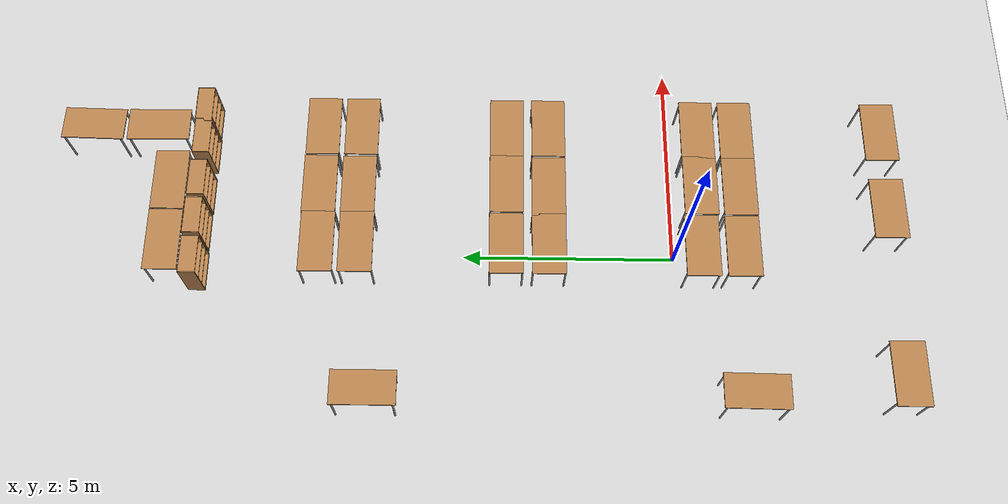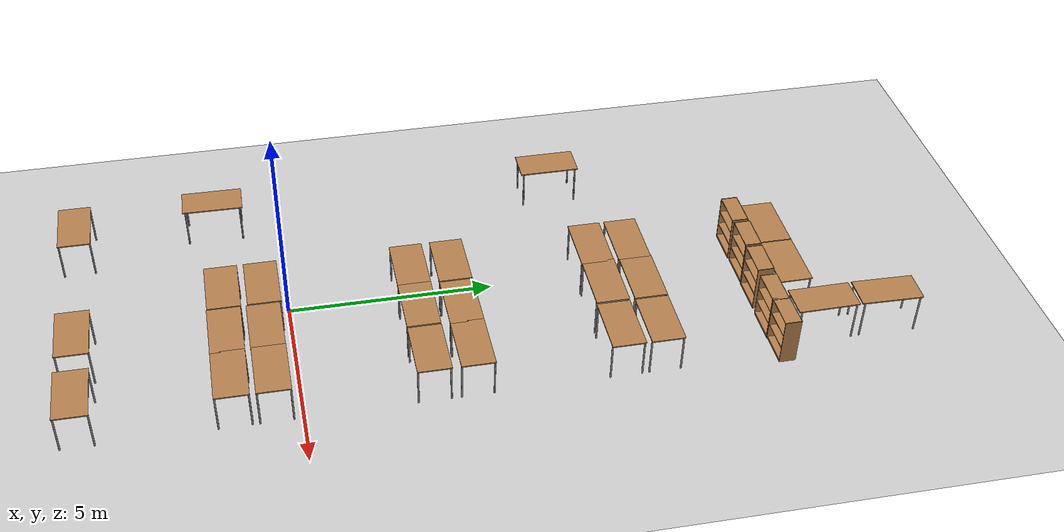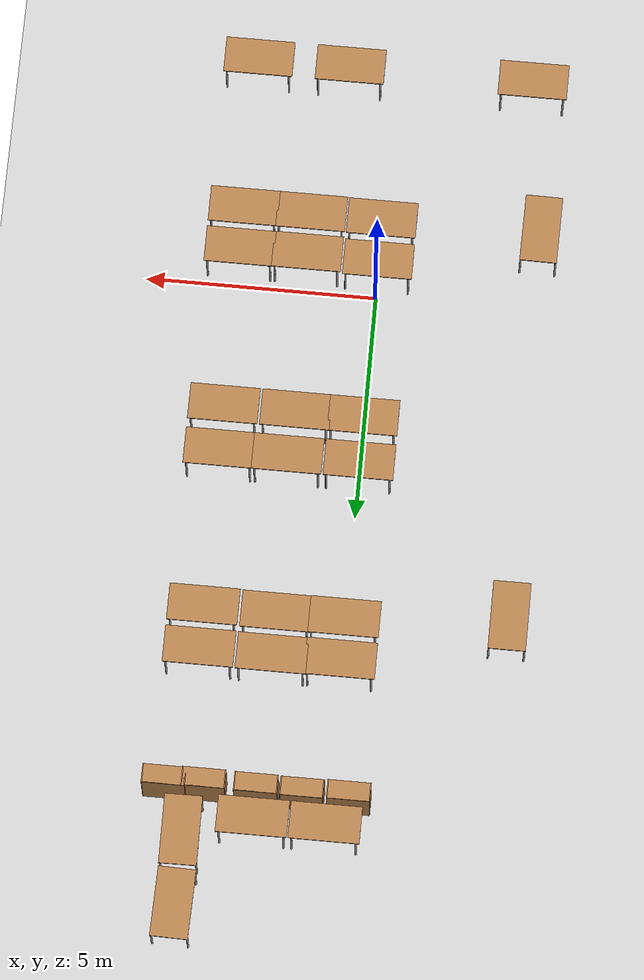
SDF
<sdf version="1.4">
 <world name="default">
  <light name="sun" type="directional">
   <pose>0 0 10 0 -0 0</pose>
   <diffuse>0.8 0.8 0.8 1</diffuse>
   <specular>0.2 0.2 0.2 1</specular>
   <attenuation>
    <range>1000</range>
    <constant>0.9</constant>
    <linear>0.01</linear>
    <quadratic>0.001</quadratic>
   </attenuation>
   <direction>-0.5 0.1 -0.9</direction>
  </light>
  <model name="ground_plane">
   <static>1</static>
   <link name="link">
    <collision name="collision">
     <geometry><plane><normal>0 0 1</normal><size>100 100</size></plane></geometry>
     <surface><friction><ode><mu>100</mu><mu2>50</mu2></ode></friction></surface>
    </collision>
    <visual name="visual">
     <cast_shadows>0</cast_shadows>
     <geometry><plane><normal>0 0 1</normal><size>100 100</size></plane></geometry>
     <material>
      <script><uri>file://media/materials/scripts/gazebo.material</uri><name>Gazebo/Grey</name></script>
     </material>
    </visual>
    <velocity_decay><linear>0</linear><angular>0</angular></velocity_decay>
   </link>
  </model>
  <physics type="ode">
   <max_step_size>0.01</max_step_size>
   <real_time_factor>1</real_time_factor>
   <real_time_update_rate>100</real_time_update_rate>
   <gravity>0 0 -9.8</gravity>
  </physics>
  <scene><ambient>0.4 0.4 0.4 1</ambient><background>0.7 0.7 0.7 1</background><shadows>1</shadows></scene>
  <spherical_coordinates>
   <surface_model>EARTH_WGS84</surface_model>
   <latitude_deg>0</latitude_deg>
   <longitude_deg>0</longitude_deg>
   <elevation>0</elevation>
   <heading_deg>0</heading_deg>
  </spherical_coordinates>
  <model name="table">
   <static>1</static>
   <link name="link">
    <collision name="surface">
     <pose>0 0 1 0 -0 0</pose>
     <geometry><box><size>1.5 0.8 0.03</size></box></geometry>
     <surface><friction><ode><mu>0.6</mu><mu2>0.6</mu2></ode></friction></surface>
    </collision>
    <visual name="visual1">
     <pose>0 0 1 0 -0 0</pose>
     <geometry><box><size>1.5 0.8 0.03</size></box></geometry>
     <material>
      <script><uri>file://media/materials/scripts/gazebo.material</uri><name>Gazebo/Wood</name></script>
     </material>
    </visual>
    <collision name="front_left_leg">
     <pose>0.68 0.38 0.5 0 -0 0</pose>
     <geometry><cylinder><radius>0.02</radius><length>1</length></cylinder></geometry>
    </collision>
    <visual name="front_left_leg">
     <pose>0.68 0.38 0.5 0 -0 0</pose>
     <geometry><cylinder><radius>0.02</radius><length>1</length></cylinder></geometry>
     <material>
      <script><uri>file://media/materials/scripts/gazebo.material</uri><name>Gazebo/Grey</name></script>
     </material>
    </visual>
    <collision name="front_right_leg">
     <pose>0.68 -0.38 0.5 0 -0 0</pose>
     <geometry><cylinder><radius>0.02</radius><length>1</length></cylinder></geometry>
    </collision>
    <visual name="front_right_leg">
     <pose>0.68 -0.38 0.5 0 -0 0</pose>
     <geometry><cylinder><radius>0.02</radius><length>1</length></cylinder></geometry>
     <material>
      <script><uri>file://media/materials/scripts/gazebo.material</uri><name>Gazebo/Grey</name></script>
     </material>
    </visual>
    <collision name="back_right_leg">
     <pose>-0.68 -0.38 0.5 0 -0 0</pose>
     <geometry><cylinder><radius>0.02</radius><length>1</length></cylinder></geometry>
    </collision>
    <visual name="back_right_leg">
     <pose>-0.68 -0.38 0.5 0 -0 0</pose>
     <geometry><cylinder><radius>0.02</radius><length>1</length></cylinder></geometry>
     <material>
      <script><uri>file://media/materials/scripts/gazebo.material</uri><name>Gazebo/Grey</name></script>
     </material>
    </visual>
    <collision name="back_left_leg">
     <pose>-0.68 0.38 0.5 0 -0 0</pose>
     <geometry><cylinder><radius>0.02</radius><length>1</length></cylinder></geometry>
    </collision>
    <visual name="back_left_leg">
     <pose>-0.68 0.38 0.5 0 -0 0</pose>
     <geometry><cylinder><radius>0.02</radius><length>1</length></cylinder></geometry>
     <material>
      <script><uri>file://media/materials/scripts/gazebo.material</uri><name>Gazebo/Grey</name></script>
     </material>
    </visual>
    <velocity_decay><linear>0</linear><angular>0</angular></velocity_decay>
   </link>
   <pose>3 -5 0 0 -0 0</pose>
  </model>
  <model name="table_0">
   <static>1</static>
   <link name="link">
    <collision name="surface">
     <pose>0 0 1 0 -0 0</pose>
     <geometry><box><size>1.5 0.8 0.03</size></box></geometry>
     <surface><friction><ode><mu>0.6</mu><mu2>0.6</mu2></ode></friction></surface>
    </collision>
    <visual name="visual1">
     <pose>0 0 1 0 -0 0</pose>
     <geometry><box><size>1.5 0.8 0.03</size></box></geometry>
     <material>
      <script><uri>file://media/materials/scripts/gazebo.material</uri><name>Gazebo/Wood</name></script>
     </material>
    </visual>
    <collision name="front_left_leg">
     <pose>0.68 0.38 0.5 0 -0 0</pose>
     <geometry><cylinder><radius>0.02</radius><length>1</length></cylinder></geometry>
    </collision>
    <visual name="front_left_leg">
     <pose>0.68 0.38 0.5 0 -0 0</pose>
     <geometry><cylinder><radius>0.02</radius><length>1</length></cylinder></geometry>
     <material>
      <script><uri>file://media/materials/scripts/gazebo.material</uri><name>Gazebo/Grey</name></script>
     </material>
    </visual>
    <collision name="front_right_leg">
     <pose>0.68 -0.38 0.5 0 -0 0</pose>
     <geometry><cylinder><radius>0.02</radius><length>1</length></cylinder></geometry>
    </collision>
    <visual name="front_right_leg">
     <pose>0.68 -0.38 0.5 0 -0 0</pose>
     <geometry><cylinder><radius>0.02</radius><length>1</length></cylinder></geometry>
     <material>
      <script><uri>file://media/materials/scripts/gazebo.material</uri><name>Gazebo/Grey</name></script>
     </material>
    </visual>
    <collision name="back_right_leg">
     <pose>-0.68 -0.38 0.5 0 -0 0</pose>
     <geometry><cylinder><radius>0.02</radius><length>1</length></cylinder></geometry>
    </collision>
    <visual name="back_right_leg">
     <pose>-0.68 -0.38 0.5 0 -0 0</pose>
     <geometry><cylinder><radius>0.02</radius><length>1</length></cylinder></geometry>
     <material>
      <script><uri>file://media/materials/scripts/gazebo.material</uri><name>Gazebo/Grey</name></script>
     </material>
    </visual>
    <collision name="back_left_leg">
     <pose>-0.68 0.38 0.5 0 -0 0</pose>
     <geometry><cylinder><radius>0.02</radius><length>1</length></cylinder></geometry>
    </collision>
    <visual name="back_left_leg">
     <pose>-0.68 0.38 0.5 0 -0 0</pose>
     <geometry><cylinder><radius>0.02</radius><length>1</length></cylinder></geometry>
     <material>
      <script><uri>file://media/materials/scripts/gazebo.material</uri><name>Gazebo/Grey</name></script>
     </material>
    </visual>
    <velocity_decay><linear>0</linear><angular>0</angular></velocity_decay>
   </link>
   <pose>1 -5 0 0 -0 0</pose>
  </model>
  <model name="table_1">
   <static>1</static>
   <link name="link">
    <collision name="surface">
     <pose>0 0 1 0 -0 0</pose>
     <geometry><box><size>1.5 0.8 0.03</size></box></geometry>
     <surface><friction><ode><mu>0.6</mu><mu2>0.6</mu2></ode></friction></surface>
    </collision>
    <visual name="visual1">
     <pose>0 0 1 0 -0 0</pose>
     <geometry><box><size>1.5 0.8 0.03</size></box></geometry>
     <material>
      <script><uri>file://media/materials/scripts/gazebo.material</uri><name>Gazebo/Wood</name></script>
     </material>
    </visual>
    <collision name="front_left_leg">
     <pose>0.68 0.38 0.5 0 -0 0</pose>
     <geometry><cylinder><radius>0.02</radius><length>1</length></cylinder></geometry>
    </collision>
    <visual name="front_left_leg">
     <pose>0.68 0.38 0.5 0 -0 0</pose>
     <geometry><cylinder><radius>0.02</radius><length>1</length></cylinder></geometry>
     <material>
      <script><uri>file://media/materials/scripts/gazebo.material</uri><name>Gazebo/Grey</name></script>
     </material>
    </visual>
    <collision name="front_right_leg">
     <pose>0.68 -0.38 0.5 0 -0 0</pose>
     <geometry><cylinder><radius>0.02</radius><length>1</length></cylinder></geometry>
    </collision>
    <visual name="front_right_leg">
     <pose>0.68 -0.38 0.5 0 -0 0</pose>
     <geometry><cylinder><radius>0.02</radius><length>1</length></cylinder></geometry>
     <material>
      <script><uri>file://media/materials/scripts/gazebo.material</uri><name>Gazebo/Grey</name></script>
     </material>
    </visual>
    <collision name="back_right_leg">
     <pose>-0.68 -0.38 0.5 0 -0 0</pose>
     <geometry><cylinder><radius>0.02</radius><length>1</length></cylinder></geometry>
    </collision>
    <visual name="back_right_leg">
     <pose>-0.68 -0.38 0.5 0 -0 0</pose>
     <geometry><cylinder><radius>0.02</radius><length>1</length></cylinder></geometry>
     <material>
      <script><uri>file://media/materials/scripts/gazebo.material</uri><name>Gazebo/Grey</name></script>
     </material>
    </visual>
    <collision name="back_left_leg">
     <pose>-0.68 0.38 0.5 0 -0 0</pose>
     <geometry><cylinder><radius>0.02</radius><length>1</length></cylinder></geometry>
    </collision>
    <visual name="back_left_leg">
     <pose>-0.68 0.38 0.5 0 -0 0</pose>
     <geometry><cylinder><radius>0.02</radius><length>1</length></cylinder></geometry>
     <material>
      <script><uri>file://media/materials/scripts/gazebo.material</uri><name>Gazebo/Grey</name></script>
     </material>
    </visual>
    <velocity_decay><linear>0</linear><angular>0</angular></velocity_decay>
   </link>
   <pose>-3 -5 0 0 -0 0</pose>
  </model>
  <model name="table_2">
   <static>1</static>
   <link name="link">
    <collision name="surface">
     <pose>0 0 1 0 -0 0</pose>
     <geometry><box><size>1.5 0.8 0.03</size></box></geometry>
     <surface><friction><ode><mu>0.6</mu><mu2>0.6</mu2></ode></friction></surface>
    </collision>
    <visual name="visual1">
     <pose>0 0 1 0 -0 0</pose>
     <geometry><box><size>1.5 0.8 0.03</size></box></geometry>
     <material>
      <script><uri>file://media/materials/scripts/gazebo.material</uri><name>Gazebo/Wood</name></script>
     </material>
    </visual>
    <collision name="front_left_leg">
     <pose>0.68 0.38 0.5 0 -0 0</pose>
     <geometry><cylinder><radius>0.02</radius><length>1</length></cylinder></geometry>
    </collision>
    <visual name="front_left_leg">
     <pose>0.68 0.38 0.5 0 -0 0</pose>
     <geometry><cylinder><radius>0.02</radius><length>1</length></cylinder></geometry>
     <material>
      <script><uri>file://media/materials/scripts/gazebo.material</uri><name>Gazebo/Grey</name></script>
     </material>
    </visual>
    <collision name="front_right_leg">
     <pose>0.68 -0.38 0.5 0 -0 0</pose>
     <geometry><cylinder><radius>0.02</radius><length>1</length></cylinder></geometry>
    </collision>
    <visual name="front_right_leg">
     <pose>0.68 -0.38 0.5 0 -0 0</pose>
     <geometry><cylinder><radius>0.02</radius><length>1</length></cylinder></geometry>
     <material>
      <script><uri>file://media/materials/scripts/gazebo.material</uri><name>Gazebo/Grey</name></script>
     </material>
    </visual>
    <collision name="back_right_leg">
     <pose>-0.68 -0.38 0.5 0 -0 0</pose>
     <geometry><cylinder><radius>0.02</radius><length>1</length></cylinder></geometry>
    </collision>
    <visual name="back_right_leg">
     <pose>-0.68 -0.38 0.5 0 -0 0</pose>
     <geometry><cylinder><radius>0.02</radius><length>1</length></cylinder></geometry>
     <material>
      <script><uri>file://media/materials/scripts/gazebo.material</uri><name>Gazebo/Grey</name></script>
     </material>
    </visual>
    <collision name="back_left_leg">
     <pose>-0.68 0.38 0.5 0 -0 0</pose>
     <geometry><cylinder><radius>0.02</radius><length>1</length></cylinder></geometry>
    </collision>
    <visual name="back_left_leg">
     <pose>-0.68 0.38 0.5 0 -0 0</pose>
     <geometry><cylinder><radius>0.02</radius><length>1</length></cylinder></geometry>
     <material>
      <script><uri>file://media/materials/scripts/gazebo.material</uri><name>Gazebo/Grey</name></script>
     </material>
    </visual>
    <velocity_decay><linear>0</linear><angular>0</angular></velocity_decay>
   </link>
   <pose>-3.44394 -1.56964 0 0 -0 1.55567</pose>
  </model>
  <model name="table_3">
   <static>1</static>
   <link name="link">
    <collision name="surface">
     <pose>0 0 1 0 -0 0</pose>
     <geometry><box><size>1.5 0.8 0.03</size></box></geometry>
     <surface><friction><ode><mu>0.6</mu><mu2>0.6</mu2></ode></friction></surface>
    </collision>
    <visual name="visual1">
     <pose>0 0 1 0 -0 0</pose>
     <geometry><box><size>1.5 0.8 0.03</size></box></geometry>
     <material>
      <script><uri>file://media/materials/scripts/gazebo.material</uri><name>Gazebo/Wood</name></script>
     </material>
    </visual>
    <collision name="front_left_leg">
     <pose>0.68 0.38 0.5 0 -0 0</pose>
     <geometry><cylinder><radius>0.02</radius><length>1</length></cylinder></geometry>
    </collision>
    <visual name="front_left_leg">
     <pose>0.68 0.38 0.5 0 -0 0</pose>
     <geometry><cylinder><radius>0.02</radius><length>1</length></cylinder></geometry>
     <material>
      <script><uri>file://media/materials/scripts/gazebo.material</uri><name>Gazebo/Grey</name></script>
     </material>
    </visual>
    <collision name="front_right_leg">
     <pose>0.68 -0.38 0.5 0 -0 0</pose>
     <geometry><cylinder><radius>0.02</radius><length>1</length></cylinder></geometry>
    </collision>
    <visual name="front_right_leg">
     <pose>0.68 -0.38 0.5 0 -0 0</pose>
     <geometry><cylinder><radius>0.02</radius><length>1</length></cylinder></geometry>
     <material>
      <script><uri>file://media/materials/scripts/gazebo.material</uri><name>Gazebo/Grey</name></script>
     </material>
    </visual>
    <collision name="back_right_leg">
     <pose>-0.68 -0.38 0.5 0 -0 0</pose>
     <geometry><cylinder><radius>0.02</radius><length>1</length></cylinder></geometry>
    </collision>
    <visual name="back_right_leg">
     <pose>-0.68 -0.38 0.5 0 -0 0</pose>
     <geometry><cylinder><radius>0.02</radius><length>1</length></cylinder></geometry>
     <material>
      <script><uri>file://media/materials/scripts/gazebo.material</uri><name>Gazebo/Grey</name></script>
     </material>
    </visual>
    <collision name="back_left_leg">
     <pose>-0.68 0.38 0.5 0 -0 0</pose>
     <geometry><cylinder><radius>0.02</radius><length>1</length></cylinder></geometry>
    </collision>
    <visual name="back_left_leg">
     <pose>-0.68 0.38 0.5 0 -0 0</pose>
     <geometry><cylinder><radius>0.02</radius><length>1</length></cylinder></geometry>
     <material>
      <script><uri>file://media/materials/scripts/gazebo.material</uri><name>Gazebo/Grey</name></script>
     </material>
    </visual>
    <velocity_decay><linear>0</linear><angular>0</angular></velocity_decay>
   </link>
   <pose>0 -1.51155 0 0 -0 0</pose>
  </model>
  <model name="table_4">
   <static>1</static>
   <link name="link">
    <collision name="surface">
     <pose>0 0 1 0 -0 0</pose>
     <geometry><box><size>1.5 0.8 0.03</size></box></geometry>
     <surface><friction><ode><mu>0.6</mu><mu2>0.6</mu2></ode></friction></surface>
    </collision>
    <visual name="visual1">
     <pose>0 0 1 0 -0 0</pose>
     <geometry><box><size>1.5 0.8 0.03</size></box></geometry>
     <material>
      <script><uri>file://media/materials/scripts/gazebo.material</uri><name>Gazebo/Wood</name></script>
     </material>
    </visual>
    <collision name="front_left_leg">
     <pose>0.68 0.38 0.5 0 -0 0</pose>
     <geometry><cylinder><radius>0.02</radius><length>1</length></cylinder></geometry>
    </collision>
    <visual name="front_left_leg">
     <pose>0.68 0.38 0.5 0 -0 0</pose>
     <geometry><cylinder><radius>0.02</radius><length>1</length></cylinder></geometry>
     <material>
      <script><uri>file://media/materials/scripts/gazebo.material</uri><name>Gazebo/Grey</name></script>
     </material>
    </visual>
    <collision name="front_right_leg">
     <pose>0.68 -0.38 0.5 0 -0 0</pose>
     <geometry><cylinder><radius>0.02</radius><length>1</length></cylinder></geometry>
    </collision>
    <visual name="front_right_leg">
     <pose>0.68 -0.38 0.5 0 -0 0</pose>
     <geometry><cylinder><radius>0.02</radius><length>1</length></cylinder></geometry>
     <material>
      <script><uri>file://media/materials/scripts/gazebo.material</uri><name>Gazebo/Grey</name></script>
     </material>
    </visual>
    <collision name="back_right_leg">
     <pose>-0.68 -0.38 0.5 0 -0 0</pose>
     <geometry><cylinder><radius>0.02</radius><length>1</length></cylinder></geometry>
    </collision>
    <visual name="back_right_leg">
     <pose>-0.68 -0.38 0.5 0 -0 0</pose>
     <geometry><cylinder><radius>0.02</radius><length>1</length></cylinder></geometry>
     <material>
      <script><uri>file://media/materials/scripts/gazebo.material</uri><name>Gazebo/Grey</name></script>
     </material>
    </visual>
    <collision name="back_left_leg">
     <pose>-0.68 0.38 0.5 0 -0 0</pose>
     <geometry><cylinder><radius>0.02</radius><length>1</length></cylinder></geometry>
    </collision>
    <visual name="back_left_leg">
     <pose>-0.68 0.38 0.5 0 -0 0</pose>
     <geometry><cylinder><radius>0.02</radius><length>1</length></cylinder></geometry>
     <material>
      <script><uri>file://media/materials/scripts/gazebo.material</uri><name>Gazebo/Grey</name></script>
     </material>
    </visual>
    <velocity_decay><linear>0</linear><angular>0</angular></velocity_decay>
   </link>
   <pose>1.53244 -1.52268 0 0 -0 0</pose>
  </model>
  <model name="table_5">
   <static>1</static>
   <link name="link">
    <collision name="surface">
     <pose>0 0 1 0 -0 0</pose>
     <geometry><box><size>1.5 0.8 0.03</size></box></geometry>
     <surface><friction><ode><mu>0.6</mu><mu2>0.6</mu2></ode></friction></surface>
    </collision>
    <visual name="visual1">
     <pose>0 0 1 0 -0 0</pose>
     <geometry><box><size>1.5 0.8 0.03</size></box></geometry>
     <material>
      <script><uri>file://media/materials/scripts/gazebo.material</uri><name>Gazebo/Wood</name></script>
     </material>
    </visual>
    <collision name="front_left_leg">
     <pose>0.68 0.38 0.5 0 -0 0</pose>
     <geometry><cylinder><radius>0.02</radius><length>1</length></cylinder></geometry>
    </collision>
    <visual name="front_left_leg">
     <pose>0.68 0.38 0.5 0 -0 0</pose>
     <geometry><cylinder><radius>0.02</radius><length>1</length></cylinder></geometry>
     <material>
      <script><uri>file://media/materials/scripts/gazebo.material</uri><name>Gazebo/Grey</name></script>
     </material>
    </visual>
    <collision name="front_right_leg">
     <pose>0.68 -0.38 0.5 0 -0 0</pose>
     <geometry><cylinder><radius>0.02</radius><length>1</length></cylinder></geometry>
    </collision>
    <visual name="front_right_leg">
     <pose>0.68 -0.38 0.5 0 -0 0</pose>
     <geometry><cylinder><radius>0.02</radius><length>1</length></cylinder></geometry>
     <material>
      <script><uri>file://media/materials/scripts/gazebo.material</uri><name>Gazebo/Grey</name></script>
     </material>
    </visual>
    <collision name="back_right_leg">
     <pose>-0.68 -0.38 0.5 0 -0 0</pose>
     <geometry><cylinder><radius>0.02</radius><length>1</length></cylinder></geometry>
    </collision>
    <visual name="back_right_leg">
     <pose>-0.68 -0.38 0.5 0 -0 0</pose>
     <geometry><cylinder><radius>0.02</radius><length>1</length></cylinder></geometry>
     <material>
      <script><uri>file://media/materials/scripts/gazebo.material</uri><name>Gazebo/Grey</name></script>
     </material>
    </visual>
    <collision name="back_left_leg">
     <pose>-0.68 0.38 0.5 0 -0 0</pose>
     <geometry><cylinder><radius>0.02</radius><length>1</length></cylinder></geometry>
    </collision>
    <visual name="back_left_leg">
     <pose>-0.68 0.38 0.5 0 -0 0</pose>
     <geometry><cylinder><radius>0.02</radius><length>1</length></cylinder></geometry>
     <material>
      <script><uri>file://media/materials/scripts/gazebo.material</uri><name>Gazebo/Grey</name></script>
     </material>
    </visual>
    <velocity_decay><linear>0</linear><angular>0</angular></velocity_decay>
   </link>
   <pose>3 -1.52315 0 0 -0 0</pose>
  </model>
  <model name="table_6">
   <static>1</static>
   <link name="link">
    <collision name="surface">
     <pose>0 0 1 0 -0 0</pose>
     <geometry><box><size>1.5 0.8 0.03</size></box></geometry>
     <surface><friction><ode><mu>0.6</mu><mu2>0.6</mu2></ode></friction></surface>
    </collision>
    <visual name="visual1">
     <pose>0 0 1 0 -0 0</pose>
     <geometry><box><size>1.5 0.8 0.03</size></box></geometry>
     <material>
      <script><uri>file://media/materials/scripts/gazebo.material</uri><name>Gazebo/Wood</name></script>
     </material>
    </visual>
    <collision name="front_left_leg">
     <pose>0.68 0.38 0.5 0 -0 0</pose>
     <geometry><cylinder><radius>0.02</radius><length>1</length></cylinder></geometry>
    </collision>
    <visual name="front_left_leg">
     <pose>0.68 0.38 0.5 0 -0 0</pose>
     <geometry><cylinder><radius>0.02</radius><length>1</length></cylinder></geometry>
     <material>
      <script><uri>file://media/materials/scripts/gazebo.material</uri><name>Gazebo/Grey</name></script>
     </material>
    </visual>
    <collision name="front_right_leg">
     <pose>0.68 -0.38 0.5 0 -0 0</pose>
     <geometry><cylinder><radius>0.02</radius><length>1</length></cylinder></geometry>
    </collision>
    <visual name="front_right_leg">
     <pose>0.68 -0.38 0.5 0 -0 0</pose>
     <geometry><cylinder><radius>0.02</radius><length>1</length></cylinder></geometry>
     <material>
      <script><uri>file://media/materials/scripts/gazebo.material</uri><name>Gazebo/Grey</name></script>
     </material>
    </visual>
    <collision name="back_right_leg">
     <pose>-0.68 -0.38 0.5 0 -0 0</pose>
     <geometry><cylinder><radius>0.02</radius><length>1</length></cylinder></geometry>
    </collision>
    <visual name="back_right_leg">
     <pose>-0.68 -0.38 0.5 0 -0 0</pose>
     <geometry><cylinder><radius>0.02</radius><length>1</length></cylinder></geometry>
     <material>
      <script><uri>file://media/materials/scripts/gazebo.material</uri><name>Gazebo/Grey</name></script>
     </material>
    </visual>
    <collision name="back_left_leg">
     <pose>-0.68 0.38 0.5 0 -0 0</pose>
     <geometry><cylinder><radius>0.02</radius><length>1</length></cylinder></geometry>
    </collision>
    <visual name="back_left_leg">
     <pose>-0.68 0.38 0.5 0 -0 0</pose>
     <geometry><cylinder><radius>0.02</radius><length>1</length></cylinder></geometry>
     <material>
      <script><uri>file://media/materials/scripts/gazebo.material</uri><name>Gazebo/Grey</name></script>
     </material>
    </visual>
    <velocity_decay><linear>0</linear><angular>0</angular></velocity_decay>
   </link>
   <pose>0 -0.562892 0 0 -0 0</pose>
  </model>
  <model name="table_7">
   <static>1</static>
   <link name="link">
    <collision name="surface">
     <pose>0 0 1 0 -0 0</pose>
     <geometry><box><size>1.5 0.8 0.03</size></box></geometry>
     <surface><friction><ode><mu>0.6</mu><mu2>0.6</mu2></ode></friction></surface>
    </collision>
    <visual name="visual1">
     <pose>0 0 1 0 -0 0</pose>
     <geometry><box><size>1.5 0.8 0.03</size></box></geometry>
     <material>
      <script><uri>file://media/materials/scripts/gazebo.material</uri><name>Gazebo/Wood</name></script>
     </material>
    </visual>
    <collision name="front_left_leg">
     <pose>0.68 0.38 0.5 0 -0 0</pose>
     <geometry><cylinder><radius>0.02</radius><length>1</length></cylinder></geometry>
    </collision>
    <visual name="front_left_leg">
     <pose>0.68 0.38 0.5 0 -0 0</pose>
     <geometry><cylinder><radius>0.02</radius><length>1</length></cylinder></geometry>
     <material>
      <script><uri>file://media/materials/scripts/gazebo.material</uri><name>Gazebo/Grey</name></script>
     </material>
    </visual>
    <collision name="front_right_leg">
     <pose>0.68 -0.38 0.5 0 -0 0</pose>
     <geometry><cylinder><radius>0.02</radius><length>1</length></cylinder></geometry>
    </collision>
    <visual name="front_right_leg">
     <pose>0.68 -0.38 0.5 0 -0 0</pose>
     <geometry><cylinder><radius>0.02</radius><length>1</length></cylinder></geometry>
     <material>
      <script><uri>file://media/materials/scripts/gazebo.material</uri><name>Gazebo/Grey</name></script>
     </material>
    </visual>
    <collision name="back_right_leg">
     <pose>-0.68 -0.38 0.5 0 -0 0</pose>
     <geometry><cylinder><radius>0.02</radius><length>1</length></cylinder></geometry>
    </collision>
    <visual name="back_right_leg">
     <pose>-0.68 -0.38 0.5 0 -0 0</pose>
     <geometry><cylinder><radius>0.02</radius><length>1</length></cylinder></geometry>
     <material>
      <script><uri>file://media/materials/scripts/gazebo.material</uri><name>Gazebo/Grey</name></script>
     </material>
    </visual>
    <collision name="back_left_leg">
     <pose>-0.68 0.38 0.5 0 -0 0</pose>
     <geometry><cylinder><radius>0.02</radius><length>1</length></cylinder></geometry>
    </collision>
    <visual name="back_left_leg">
     <pose>-0.68 0.38 0.5 0 -0 0</pose>
     <geometry><cylinder><radius>0.02</radius><length>1</length></cylinder></geometry>
     <material>
      <script><uri>file://media/materials/scripts/gazebo.material</uri><name>Gazebo/Grey</name></script>
     </material>
    </visual>
    <velocity_decay><linear>0</linear><angular>0</angular></velocity_decay>
   </link>
   <pose>1.5385 -0.598204 0 0 -0 0</pose>
  </model>
  <model name="table_8">
   <static>1</static>
   <link name="link">
    <collision name="surface">
     <pose>0 0 1 0 -0 0</pose>
     <geometry><box><size>1.5 0.8 0.03</size></box></geometry>
     <surface><friction><ode><mu>0.6</mu><mu2>0.6</mu2></ode></friction></surface>
    </collision>
    <visual name="visual1">
     <pose>0 0 1 0 -0 0</pose>
     <geometry><box><size>1.5 0.8 0.03</size></box></geometry>
     <material>
      <script><uri>file://media/materials/scripts/gazebo.material</uri><name>Gazebo/Wood</name></script>
     </material>
    </visual>
    <collision name="front_left_leg">
     <pose>0.68 0.38 0.5 0 -0 0</pose>
     <geometry><cylinder><radius>0.02</radius><length>1</length></cylinder></geometry>
    </collision>
    <visual name="front_left_leg">
     <pose>0.68 0.38 0.5 0 -0 0</pose>
     <geometry><cylinder><radius>0.02</radius><length>1</length></cylinder></geometry>
     <material>
      <script><uri>file://media/materials/scripts/gazebo.material</uri><name>Gazebo/Grey</name></script>
     </material>
    </visual>
    <collision name="front_right_leg">
     <pose>0.68 -0.38 0.5 0 -0 0</pose>
     <geometry><cylinder><radius>0.02</radius><length>1</length></cylinder></geometry>
    </collision>
    <visual name="front_right_leg">
     <pose>0.68 -0.38 0.5 0 -0 0</pose>
     <geometry><cylinder><radius>0.02</radius><length>1</length></cylinder></geometry>
     <material>
      <script><uri>file://media/materials/scripts/gazebo.material</uri><name>Gazebo/Grey</name></script>
     </material>
    </visual>
    <collision name="back_right_leg">
     <pose>-0.68 -0.38 0.5 0 -0 0</pose>
     <geometry><cylinder><radius>0.02</radius><length>1</length></cylinder></geometry>
    </collision>
    <visual name="back_right_leg">
     <pose>-0.68 -0.38 0.5 0 -0 0</pose>
     <geometry><cylinder><radius>0.02</radius><length>1</length></cylinder></geometry>
     <material>
      <script><uri>file://media/materials/scripts/gazebo.material</uri><name>Gazebo/Grey</name></script>
     </material>
    </visual>
    <collision name="back_left_leg">
     <pose>-0.68 0.38 0.5 0 -0 0</pose>
     <geometry><cylinder><radius>0.02</radius><length>1</length></cylinder></geometry>
    </collision>
    <visual name="back_left_leg">
     <pose>-0.68 0.38 0.5 0 -0 0</pose>
     <geometry><cylinder><radius>0.02</radius><length>1</length></cylinder></geometry>
     <material>
      <script><uri>file://media/materials/scripts/gazebo.material</uri><name>Gazebo/Grey</name></script>
     </material>
    </visual>
    <velocity_decay><linear>0</linear><angular>0</angular></velocity_decay>
   </link>
   <pose>3 -0.592507 0 0 -0 0</pose>
  </model>
  <model name="table_9">
   <static>1</static>
   <link name="link">
    <collision name="surface">
     <pose>0 0 1 0 -0 0</pose>
     <geometry><box><size>1.5 0.8 0.03</size></box></geometry>
     <surface><friction><ode><mu>0.6</mu><mu2>0.6</mu2></ode></friction></surface>
    </collision>
    <visual name="visual1">
     <pose>0 0 1 0 -0 0</pose>
     <geometry><box><size>1.5 0.8 0.03</size></box></geometry>
     <material>
      <script><uri>file://media/materials/scripts/gazebo.material</uri><name>Gazebo/Wood</name></script>
     </material>
    </visual>
    <collision name="front_left_leg">
     <pose>0.68 0.38 0.5 0 -0 0</pose>
     <geometry><cylinder><radius>0.02</radius><length>1</length></cylinder></geometry>
    </collision>
    <visual name="front_left_leg">
     <pose>0.68 0.38 0.5 0 -0 0</pose>
     <geometry><cylinder><radius>0.02</radius><length>1</length></cylinder></geometry>
     <material>
      <script><uri>file://media/materials/scripts/gazebo.material</uri><name>Gazebo/Grey</name></script>
     </material>
    </visual>
    <collision name="front_right_leg">
     <pose>0.68 -0.38 0.5 0 -0 0</pose>
     <geometry><cylinder><radius>0.02</radius><length>1</length></cylinder></geometry>
    </collision>
    <visual name="front_right_leg">
     <pose>0.68 -0.38 0.5 0 -0 0</pose>
     <geometry><cylinder><radius>0.02</radius><length>1</length></cylinder></geometry>
     <material>
      <script><uri>file://media/materials/scripts/gazebo.material</uri><name>Gazebo/Grey</name></script>
     </material>
    </visual>
    <collision name="back_right_leg">
     <pose>-0.68 -0.38 0.5 0 -0 0</pose>
     <geometry><cylinder><radius>0.02</radius><length>1</length></cylinder></geometry>
    </collision>
    <visual name="back_right_leg">
     <pose>-0.68 -0.38 0.5 0 -0 0</pose>
     <geometry><cylinder><radius>0.02</radius><length>1</length></cylinder></geometry>
     <material>
      <script><uri>file://media/materials/scripts/gazebo.material</uri><name>Gazebo/Grey</name></script>
     </material>
    </visual>
    <collision name="back_left_leg">
     <pose>-0.68 0.38 0.5 0 -0 0</pose>
     <geometry><cylinder><radius>0.02</radius><length>1</length></cylinder></geometry>
    </collision>
    <visual name="back_left_leg">
     <pose>-0.68 0.38 0.5 0 -0 0</pose>
     <geometry><cylinder><radius>0.02</radius><length>1</length></cylinder></geometry>
     <material>
      <script><uri>file://media/materials/scripts/gazebo.material</uri><name>Gazebo/Grey</name></script>
     </material>
    </visual>
    <velocity_decay><linear>0</linear><angular>0</angular></velocity_decay>
   </link>
   <pose>3 3 0 0 -0 0</pose>
  </model>
  <model name="table_10">
   <static>1</static>
   <link name="link">
    <collision name="surface">
     <pose>0 0 1 0 -0 0</pose>
     <geometry><box><size>1.5 0.8 0.03</size></box></geometry>
     <surface><friction><ode><mu>0.6</mu><mu2>0.6</mu2></ode></friction></surface>
    </collision>
    <visual name="visual1">
     <pose>0 0 1 0 -0 0</pose>
     <geometry><box><size>1.5 0.8 0.03</size></box></geometry>
     <material>
      <script><uri>file://media/materials/scripts/gazebo.material</uri><name>Gazebo/Wood</name></script>
     </material>
    </visual>
    <collision name="front_left_leg">
     <pose>0.68 0.38 0.5 0 -0 0</pose>
     <geometry><cylinder><radius>0.02</radius><length>1</length></cylinder></geometry>
    </collision>
    <visual name="front_left_leg">
     <pose>0.68 0.38 0.5 0 -0 0</pose>
     <geometry><cylinder><radius>0.02</radius><length>1</length></cylinder></geometry>
     <material>
      <script><uri>file://media/materials/scripts/gazebo.material</uri><name>Gazebo/Grey</name></script>
     </material>
    </visual>
    <collision name="front_right_leg">
     <pose>0.68 -0.38 0.5 0 -0 0</pose>
     <geometry><cylinder><radius>0.02</radius><length>1</length></cylinder></geometry>
    </collision>
    <visual name="front_right_leg">
     <pose>0.68 -0.38 0.5 0 -0 0</pose>
     <geometry><cylinder><radius>0.02</radius><length>1</length></cylinder></geometry>
     <material>
      <script><uri>file://media/materials/scripts/gazebo.material</uri><name>Gazebo/Grey</name></script>
     </material>
    </visual>
    <collision name="back_right_leg">
     <pose>-0.68 -0.38 0.5 0 -0 0</pose>
     <geometry><cylinder><radius>0.02</radius><length>1</length></cylinder></geometry>
    </collision>
    <visual name="back_right_leg">
     <pose>-0.68 -0.38 0.5 0 -0 0</pose>
     <geometry><cylinder><radius>0.02</radius><length>1</length></cylinder></geometry>
     <material>
      <script><uri>file://media/materials/scripts/gazebo.material</uri><name>Gazebo/Grey</name></script>
     </material>
    </visual>
    <collision name="back_left_leg">
     <pose>-0.68 0.38 0.5 0 -0 0</pose>
     <geometry><cylinder><radius>0.02</radius><length>1</length></cylinder></geometry>
    </collision>
    <visual name="back_left_leg">
     <pose>-0.68 0.38 0.5 0 -0 0</pose>
     <geometry><cylinder><radius>0.02</radius><length>1</length></cylinder></geometry>
     <material>
      <script><uri>file://media/materials/scripts/gazebo.material</uri><name>Gazebo/Grey</name></script>
     </material>
    </visual>
    <velocity_decay><linear>0</linear><angular>0</angular></velocity_decay>
   </link>
   <pose>1.45547 3 0 0 -0 0</pose>
  </model>
  <model name="table_11">
   <static>1</static>
   <link name="link">
    <collision name="surface">
     <pose>0 0 1 0 -0 0</pose>
     <geometry><box><size>1.5 0.8 0.03</size></box></geometry>
     <surface><friction><ode><mu>0.6</mu><mu2>0.6</mu2></ode></friction></surface>
    </collision>
    <visual name="visual1">
     <pose>0 0 1 0 -0 0</pose>
     <geometry><box><size>1.5 0.8 0.03</size></box></geometry>
     <material>
      <script><uri>file://media/materials/scripts/gazebo.material</uri><name>Gazebo/Wood</name></script>
     </material>
    </visual>
    <collision name="front_left_leg">
     <pose>0.68 0.38 0.5 0 -0 0</pose>
     <geometry><cylinder><radius>0.02</radius><length>1</length></cylinder></geometry>
    </collision>
    <visual name="front_left_leg">
     <pose>0.68 0.38 0.5 0 -0 0</pose>
     <geometry><cylinder><radius>0.02</radius><length>1</length></cylinder></geometry>
     <material>
      <script><uri>file://media/materials/scripts/gazebo.material</uri><name>Gazebo/Grey</name></script>
     </material>
    </visual>
    <collision name="front_right_leg">
     <pose>0.68 -0.38 0.5 0 -0 0</pose>
     <geometry><cylinder><radius>0.02</radius><length>1</length></cylinder></geometry>
    </collision>
    <visual name="front_right_leg">
     <pose>0.68 -0.38 0.5 0 -0 0</pose>
     <geometry><cylinder><radius>0.02</radius><length>1</length></cylinder></geometry>
     <material>
      <script><uri>file://media/materials/scripts/gazebo.material</uri><name>Gazebo/Grey</name></script>
     </material>
    </visual>
    <collision name="back_right_leg">
     <pose>-0.68 -0.38 0.5 0 -0 0</pose>
     <geometry><cylinder><radius>0.02</radius><length>1</length></cylinder></geometry>
    </collision>
    <visual name="back_right_leg">
     <pose>-0.68 -0.38 0.5 0 -0 0</pose>
     <geometry><cylinder><radius>0.02</radius><length>1</length></cylinder></geometry>
     <material>
      <script><uri>file://media/materials/scripts/gazebo.material</uri><name>Gazebo/Grey</name></script>
     </material>
    </visual>
    <collision name="back_left_leg">
     <pose>-0.68 0.38 0.5 0 -0 0</pose>
     <geometry><cylinder><radius>0.02</radius><length>1</length></cylinder></geometry>
    </collision>
    <visual name="back_left_leg">
     <pose>-0.68 0.38 0.5 0 -0 0</pose>
     <geometry><cylinder><radius>0.02</radius><length>1</length></cylinder></geometry>
     <material>
      <script><uri>file://media/materials/scripts/gazebo.material</uri><name>Gazebo/Grey</name></script>
     </material>
    </visual>
    <velocity_decay><linear>0</linear><angular>0</angular></velocity_decay>
   </link>
   <pose>0 3 0 0 -0 0</pose>
  </model>
  <model name="table_12">
   <static>1</static>
   <link name="link">
    <collision name="surface">
     <pose>0 0 1 0 -0 0</pose>
     <geometry><box><size>1.5 0.8 0.03</size></box></geometry>
     <surface><friction><ode><mu>0.6</mu><mu2>0.6</mu2></ode></friction></surface>
    </collision>
    <visual name="visual1">
     <pose>0 0 1 0 -0 0</pose>
     <geometry><box><size>1.5 0.8 0.03</size></box></geometry>
     <material>
      <script><uri>file://media/materials/scripts/gazebo.material</uri><name>Gazebo/Wood</name></script>
     </material>
    </visual>
    <collision name="front_left_leg">
     <pose>0.68 0.38 0.5 0 -0 0</pose>
     <geometry><cylinder><radius>0.02</radius><length>1</length></cylinder></geometry>
    </collision>
    <visual name="front_left_leg">
     <pose>0.68 0.38 0.5 0 -0 0</pose>
     <geometry><cylinder><radius>0.02</radius><length>1</length></cylinder></geometry>
     <material>
      <script><uri>file://media/materials/scripts/gazebo.material</uri><name>Gazebo/Grey</name></script>
     </material>
    </visual>
    <collision name="front_right_leg">
     <pose>0.68 -0.38 0.5 0 -0 0</pose>
     <geometry><cylinder><radius>0.02</radius><length>1</length></cylinder></geometry>
    </collision>
    <visual name="front_right_leg">
     <pose>0.68 -0.38 0.5 0 -0 0</pose>
     <geometry><cylinder><radius>0.02</radius><length>1</length></cylinder></geometry>
     <material>
      <script><uri>file://media/materials/scripts/gazebo.material</uri><name>Gazebo/Grey</name></script>
     </material>
    </visual>
    <collision name="back_right_leg">
     <pose>-0.68 -0.38 0.5 0 -0 0</pose>
     <geometry><cylinder><radius>0.02</radius><length>1</length></cylinder></geometry>
    </collision>
    <visual name="back_right_leg">
     <pose>-0.68 -0.38 0.5 0 -0 0</pose>
     <geometry><cylinder><radius>0.02</radius><length>1</length></cylinder></geometry>
     <material>
      <script><uri>file://media/materials/scripts/gazebo.material</uri><name>Gazebo/Grey</name></script>
     </material>
    </visual>
    <collision name="back_left_leg">
     <pose>-0.68 0.38 0.5 0 -0 0</pose>
     <geometry><cylinder><radius>0.02</radius><length>1</length></cylinder></geometry>
    </collision>
    <visual name="back_left_leg">
     <pose>-0.68 0.38 0.5 0 -0 0</pose>
     <geometry><cylinder><radius>0.02</radius><length>1</length></cylinder></geometry>
     <material>
      <script><uri>file://media/materials/scripts/gazebo.material</uri><name>Gazebo/Grey</name></script>
     </material>
    </visual>
    <velocity_decay><linear>0</linear><angular>0</angular></velocity_decay>
   </link>
   <pose>3 4 0 0 -0 0</pose>
  </model>
  <model name="table_13">
   <static>1</static>
   <link name="link">
    <collision name="surface">
     <pose>0 0 1 0 -0 0</pose>
     <geometry><box><size>1.5 0.8 0.03</size></box></geometry>
     <surface><friction><ode><mu>0.6</mu><mu2>0.6</mu2></ode></friction></surface>
    </collision>
    <visual name="visual1">
     <pose>0 0 1 0 -0 0</pose>
     <geometry><box><size>1.5 0.8 0.03</size></box></geometry>
     <material>
      <script><uri>file://media/materials/scripts/gazebo.material</uri><name>Gazebo/Wood</name></script>
     </material>
    </visual>
    <collision name="front_left_leg">
     <pose>0.68 0.38 0.5 0 -0 0</pose>
     <geometry><cylinder><radius>0.02</radius><length>1</length></cylinder></geometry>
    </collision>
    <visual name="front_left_leg">
     <pose>0.68 0.38 0.5 0 -0 0</pose>
     <geometry><cylinder><radius>0.02</radius><length>1</length></cylinder></geometry>
     <material>
      <script><uri>file://media/materials/scripts/gazebo.material</uri><name>Gazebo/Grey</name></script>
     </material>
    </visual>
    <collision name="front_right_leg">
     <pose>0.68 -0.38 0.5 0 -0 0</pose>
     <geometry><cylinder><radius>0.02</radius><length>1</length></cylinder></geometry>
    </collision>
    <visual name="front_right_leg">
     <pose>0.68 -0.38 0.5 0 -0 0</pose>
     <geometry><cylinder><radius>0.02</radius><length>1</length></cylinder></geometry>
     <material>
      <script><uri>file://media/materials/scripts/gazebo.material</uri><name>Gazebo/Grey</name></script>
     </material>
    </visual>
    <collision name="back_right_leg">
     <pose>-0.68 -0.38 0.5 0 -0 0</pose>
     <geometry><cylinder><radius>0.02</radius><length>1</length></cylinder></geometry>
    </collision>
    <visual name="back_right_leg">
     <pose>-0.68 -0.38 0.5 0 -0 0</pose>
     <geometry><cylinder><radius>0.02</radius><length>1</length></cylinder></geometry>
     <material>
      <script><uri>file://media/materials/scripts/gazebo.material</uri><name>Gazebo/Grey</name></script>
     </material>
    </visual>
    <collision name="back_left_leg">
     <pose>-0.68 0.38 0.5 0 -0 0</pose>
     <geometry><cylinder><radius>0.02</radius><length>1</length></cylinder></geometry>
    </collision>
    <visual name="back_left_leg">
     <pose>-0.68 0.38 0.5 0 -0 0</pose>
     <geometry><cylinder><radius>0.02</radius><length>1</length></cylinder></geometry>
     <material>
      <script><uri>file://media/materials/scripts/gazebo.material</uri><name>Gazebo/Grey</name></script>
     </material>
    </visual>
    <velocity_decay><linear>0</linear><angular>0</angular></velocity_decay>
   </link>
   <pose>1.53675 4 0 0 -0 0</pose>
  </model>
  <model name="table_14">
   <static>1</static>
   <link name="link">
    <collision name="surface">
     <pose>0 0 1 0 -0 0</pose>
     <geometry><box><size>1.5 0.8 0.03</size></box></geometry>
     <surface><friction><ode><mu>0.6</mu><mu2>0.6</mu2></ode></friction></surface>
    </collision>
    <visual name="visual1">
     <pose>0 0 1 0 -0 0</pose>
     <geometry><box><size>1.5 0.8 0.03</size></box></geometry>
     <material>
      <script><uri>file://media/materials/scripts/gazebo.material</uri><name>Gazebo/Wood</name></script>
     </material>
    </visual>
    <collision name="front_left_leg">
     <pose>0.68 0.38 0.5 0 -0 0</pose>
     <geometry><cylinder><radius>0.02</radius><length>1</length></cylinder></geometry>
    </collision>
    <visual name="front_left_leg">
     <pose>0.68 0.38 0.5 0 -0 0</pose>
     <geometry><cylinder><radius>0.02</radius><length>1</length></cylinder></geometry>
     <material>
      <script><uri>file://media/materials/scripts/gazebo.material</uri><name>Gazebo/Grey</name></script>
     </material>
    </visual>
    <collision name="front_right_leg">
     <pose>0.68 -0.38 0.5 0 -0 0</pose>
     <geometry><cylinder><radius>0.02</radius><length>1</length></cylinder></geometry>
    </collision>
    <visual name="front_right_leg">
     <pose>0.68 -0.38 0.5 0 -0 0</pose>
     <geometry><cylinder><radius>0.02</radius><length>1</length></cylinder></geometry>
     <material>
      <script><uri>file://media/materials/scripts/gazebo.material</uri><name>Gazebo/Grey</name></script>
     </material>
    </visual>
    <collision name="back_right_leg">
     <pose>-0.68 -0.38 0.5 0 -0 0</pose>
     <geometry><cylinder><radius>0.02</radius><length>1</length></cylinder></geometry>
    </collision>
    <visual name="back_right_leg">
     <pose>-0.68 -0.38 0.5 0 -0 0</pose>
     <geometry><cylinder><radius>0.02</radius><length>1</length></cylinder></geometry>
     <material>
      <script><uri>file://media/materials/scripts/gazebo.material</uri><name>Gazebo/Grey</name></script>
     </material>
    </visual>
    <collision name="back_left_leg">
     <pose>-0.68 0.38 0.5 0 -0 0</pose>
     <geometry><cylinder><radius>0.02</radius><length>1</length></cylinder></geometry>
    </collision>
    <visual name="back_left_leg">
     <pose>-0.68 0.38 0.5 0 -0 0</pose>
     <geometry><cylinder><radius>0.02</radius><length>1</length></cylinder></geometry>
     <material>
      <script><uri>file://media/materials/scripts/gazebo.material</uri><name>Gazebo/Grey</name></script>
     </material>
    </visual>
    <velocity_decay><linear>0</linear><angular>0</angular></velocity_decay>
   </link>
   <pose>0 4 0 0 -0 0</pose>
  </model>
  <model name="table_15">
   <static>1</static>
   <link name="link">
    <collision name="surface">
     <pose>0 0 1 0 -0 0</pose>
     <geometry><box><size>1.5 0.8 0.03</size></box></geometry>
     <surface><friction><ode><mu>0.6</mu><mu2>0.6</mu2></ode></friction></surface>
    </collision>
    <visual name="visual1">
     <pose>0 0 1 0 -0 0</pose>
     <geometry><box><size>1.5 0.8 0.03</size></box></geometry>
     <material>
      <script><uri>file://media/materials/scripts/gazebo.material</uri><name>Gazebo/Wood</name></script>
     </material>
    </visual>
    <collision name="front_left_leg">
     <pose>0.68 0.38 0.5 0 -0 0</pose>
     <geometry><cylinder><radius>0.02</radius><length>1</length></cylinder></geometry>
    </collision>
    <visual name="front_left_leg">
     <pose>0.68 0.38 0.5 0 -0 0</pose>
     <geometry><cylinder><radius>0.02</radius><length>1</length></cylinder></geometry>
     <material>
      <script><uri>file://media/materials/scripts/gazebo.material</uri><name>Gazebo/Grey</name></script>
     </material>
    </visual>
    <collision name="front_right_leg">
     <pose>0.68 -0.38 0.5 0 -0 0</pose>
     <geometry><cylinder><radius>0.02</radius><length>1</length></cylinder></geometry>
    </collision>
    <visual name="front_right_leg">
     <pose>0.68 -0.38 0.5 0 -0 0</pose>
     <geometry><cylinder><radius>0.02</radius><length>1</length></cylinder></geometry>
     <material>
      <script><uri>file://media/materials/scripts/gazebo.material</uri><name>Gazebo/Grey</name></script>
     </material>
    </visual>
    <collision name="back_right_leg">
     <pose>-0.68 -0.38 0.5 0 -0 0</pose>
     <geometry><cylinder><radius>0.02</radius><length>1</length></cylinder></geometry>
    </collision>
    <visual name="back_right_leg">
     <pose>-0.68 -0.38 0.5 0 -0 0</pose>
     <geometry><cylinder><radius>0.02</radius><length>1</length></cylinder></geometry>
     <material>
      <script><uri>file://media/materials/scripts/gazebo.material</uri><name>Gazebo/Grey</name></script>
     </material>
    </visual>
    <collision name="back_left_leg">
     <pose>-0.68 0.38 0.5 0 -0 0</pose>
     <geometry><cylinder><radius>0.02</radius><length>1</length></cylinder></geometry>
    </collision>
    <visual name="back_left_leg">
     <pose>-0.68 0.38 0.5 0 -0 0</pose>
     <geometry><cylinder><radius>0.02</radius><length>1</length></cylinder></geometry>
     <material>
      <script><uri>file://media/materials/scripts/gazebo.material</uri><name>Gazebo/Grey</name></script>
     </material>
    </visual>
    <velocity_decay><linear>0</linear><angular>0</angular></velocity_decay>
   </link>
   <pose>-3.47187 7.16599 0 0 -0 1.56969</pose>
  </model>
  <model name="bookshelf">
   <static>1</static>
   <link name="link">
    <inertial><mass>1</mass></inertial>
    <collision name="back">
     <pose>0 0.005 0.6 0 -0 0</pose>
     <geometry><box><size>0.9 0.01 1.2</size></box></geometry>
    </collision>
    <visual name="visual1">
     <pose>0 0.005 0.6 0 -0 0</pose>
     <geometry><box><size>0.9 0.01 1.2</size></box></geometry>
     <material>
      <script><uri>file://media/materials/scripts/gazebo.material</uri><name>Gazebo/Wood</name></script>
     </material>
    </visual>
    <collision name="left_side">
     <pose>0.45 -0.195 0.6 0 -0 0</pose>
     <geometry><box><size>0.02 0.4 1.2</size></box></geometry>
    </collision>
    <visual name="visual2">
     <pose>0.45 -0.195 0.6 0 -0 0</pose>
     <geometry><box><size>0.02 0.4 1.2</size></box></geometry>
     <material>
      <script><uri>file://media/materials/scripts/gazebo.material</uri><name>Gazebo/Wood</name></script>
     </material>
    </visual>
    <collision name="right_side">
     <pose>-0.45 -0.195 0.6 0 -0 0</pose>
     <geometry><box><size>0.02 0.4 1.2</size></box></geometry>
    </collision>
    <visual name="visual3">
     <pose>-0.45 -0.195 0.6 0 -0 0</pose>
     <geometry><box><size>0.02 0.4 1.2</size></box></geometry>
     <material>
      <script><uri>file://media/materials/scripts/gazebo.material</uri><name>Gazebo/Wood</name></script>
     </material>
    </visual>
    <collision name="bottom">
     <pose>0 -0.195 0.03 0 -0 0</pose>
     <geometry><box><size>0.88 0.4 0.06</size></box></geometry>
    </collision>
    <visual name="visual4">
     <pose>0 -0.195 0.03 0 -0 0</pose>
     <geometry><box><size>0.88 0.4 0.06</size></box></geometry>
     <material>
      <script><uri>file://media/materials/scripts/gazebo.material</uri><name>Gazebo/Wood</name></script>
     </material>
    </visual>
    <collision name="top">
     <pose>0 -0.195 1.19 0 -0 0</pose>
     <geometry><box><size>0.88 0.4 0.02</size></box></geometry>
    </collision>
    <visual name="visual5">
     <pose>0 -0.195 1.19 0 -0 0</pose>
     <geometry><box><size>0.88 0.4 0.02</size></box></geometry>
     <material>
      <script><uri>file://media/materials/scripts/gazebo.material</uri><name>Gazebo/Wood</name></script>
     </material>
    </visual>
    <collision name="low_shelf">
     <pose>0 -0.195 0.43 0 -0 0</pose>
     <geometry><box><size>0.88 0.4 0.02</size></box></geometry>
    </collision>
    <visual name="visual6">
     <pose>0 -0.195 0.43 0 -0 0</pose>
     <geometry><box><size>0.88 0.4 0.02</size></box></geometry>
     <material>
      <script><uri>file://media/materials/scripts/gazebo.material</uri><name>Gazebo/Wood</name></script>
     </material>
    </visual>
    <collision name="high_shelf">
     <pose>0 -0.195 0.8 0 -0 0</pose>
     <geometry><box><size>0.88 0.4 0.02</size></box></geometry>
    </collision>
    <visual name="visual7">
     <pose>0 -0.195 0.8 0 -0 0</pose>
     <geometry><box><size>0.88 0.4 0.02</size></box></geometry>
     <material>
      <script><uri>file://media/materials/scripts/gazebo.material</uri><name>Gazebo/Wood</name></script>
     </material>
    </visual>
    <velocity_decay><linear>0</linear><angular>0</angular></velocity_decay>
   </link>
   <pose>2.61965 11.5036 0 0 -0 0</pose>
  </model>
  <model name="table_16">
   <static>1</static>
   <link name="link">
    <collision name="surface">
     <pose>0 0 1 0 -0 0</pose>
     <geometry><box><size>1.5 0.8 0.03</size></box></geometry>
     <surface><friction><ode><mu>0.6</mu><mu2>0.6</mu2></ode></friction></surface>
    </collision>
    <visual name="visual1">
     <pose>0 0 1 0 -0 0</pose>
     <geometry><box><size>1.5 0.8 0.03</size></box></geometry>
     <material>
      <script><uri>file://media/materials/scripts/gazebo.material</uri><name>Gazebo/Wood</name></script>
     </material>
    </visual>
    <collision name="front_left_leg">
     <pose>0.68 0.38 0.5 0 -0 0</pose>
     <geometry><cylinder><radius>0.02</radius><length>1</length></cylinder></geometry>
    </collision>
    <visual name="front_left_leg">
     <pose>0.68 0.38 0.5 0 -0 0</pose>
     <geometry><cylinder><radius>0.02</radius><length>1</length></cylinder></geometry>
     <material>
      <script><uri>file://media/materials/scripts/gazebo.material</uri><name>Gazebo/Grey</name></script>
     </material>
    </visual>
    <collision name="front_right_leg">
     <pose>0.68 -0.38 0.5 0 -0 0</pose>
     <geometry><cylinder><radius>0.02</radius><length>1</length></cylinder></geometry>
    </collision>
    <visual name="front_right_leg">
     <pose>0.68 -0.38 0.5 0 -0 0</pose>
     <geometry><cylinder><radius>0.02</radius><length>1</length></cylinder></geometry>
     <material>
      <script><uri>file://media/materials/scripts/gazebo.material</uri><name>Gazebo/Grey</name></script>
     </material>
    </visual>
    <collision name="back_right_leg">
     <pose>-0.68 -0.38 0.5 0 -0 0</pose>
     <geometry><cylinder><radius>0.02</radius><length>1</length></cylinder></geometry>
    </collision>
    <visual name="back_right_leg">
     <pose>-0.68 -0.38 0.5 0 -0 0</pose>
     <geometry><cylinder><radius>0.02</radius><length>1</length></cylinder></geometry>
     <material>
      <script><uri>file://media/materials/scripts/gazebo.material</uri><name>Gazebo/Grey</name></script>
     </material>
    </visual>
    <collision name="back_left_leg">
     <pose>-0.68 0.38 0.5 0 -0 0</pose>
     <geometry><cylinder><radius>0.02</radius><length>1</length></cylinder></geometry>
    </collision>
    <visual name="back_left_leg">
     <pose>-0.68 0.38 0.5 0 -0 0</pose>
     <geometry><cylinder><radius>0.02</radius><length>1</length></cylinder></geometry>
     <material>
      <script><uri>file://media/materials/scripts/gazebo.material</uri><name>Gazebo/Grey</name></script>
     </material>
    </visual>
    <velocity_decay><linear>0</linear><angular>0</angular></velocity_decay>
   </link>
   <pose>3 7.49371 0 0 -0 0</pose>
  </model>
  <model name="table_17">
   <static>1</static>
   <link name="link">
    <collision name="surface">
     <pose>0 0 1 0 -0 0</pose>
     <geometry><box><size>1.5 0.8 0.03</size></box></geometry>
     <surface><friction><ode><mu>0.6</mu><mu2>0.6</mu2></ode></friction></surface>
    </collision>
    <visual name="visual1">
     <pose>0 0 1 0 -0 0</pose>
     <geometry><box><size>1.5 0.8 0.03</size></box></geometry>
     <material>
      <script><uri>file://media/materials/scripts/gazebo.material</uri><name>Gazebo/Wood</name></script>
     </material>
    </visual>
    <collision name="front_left_leg">
     <pose>0.68 0.38 0.5 0 -0 0</pose>
     <geometry><cylinder><radius>0.02</radius><length>1</length></cylinder></geometry>
    </collision>
    <visual name="front_left_leg">
     <pose>0.68 0.38 0.5 0 -0 0</pose>
     <geometry><cylinder><radius>0.02</radius><length>1</length></cylinder></geometry>
     <material>
      <script><uri>file://media/materials/scripts/gazebo.material</uri><name>Gazebo/Grey</name></script>
     </material>
    </visual>
    <collision name="front_right_leg">
     <pose>0.68 -0.38 0.5 0 -0 0</pose>
     <geometry><cylinder><radius>0.02</radius><length>1</length></cylinder></geometry>
    </collision>
    <visual name="front_right_leg">
     <pose>0.68 -0.38 0.5 0 -0 0</pose>
     <geometry><cylinder><radius>0.02</radius><length>1</length></cylinder></geometry>
     <material>
      <script><uri>file://media/materials/scripts/gazebo.material</uri><name>Gazebo/Grey</name></script>
     </material>
    </visual>
    <collision name="back_right_leg">
     <pose>-0.68 -0.38 0.5 0 -0 0</pose>
     <geometry><cylinder><radius>0.02</radius><length>1</length></cylinder></geometry>
    </collision>
    <visual name="back_right_leg">
     <pose>-0.68 -0.38 0.5 0 -0 0</pose>
     <geometry><cylinder><radius>0.02</radius><length>1</length></cylinder></geometry>
     <material>
      <script><uri>file://media/materials/scripts/gazebo.material</uri><name>Gazebo/Grey</name></script>
     </material>
    </visual>
    <collision name="back_left_leg">
     <pose>-0.68 0.38 0.5 0 -0 0</pose>
     <geometry><cylinder><radius>0.02</radius><length>1</length></cylinder></geometry>
    </collision>
    <visual name="back_left_leg">
     <pose>-0.68 0.38 0.5 0 -0 0</pose>
     <geometry><cylinder><radius>0.02</radius><length>1</length></cylinder></geometry>
     <material>
      <script><uri>file://media/materials/scripts/gazebo.material</uri><name>Gazebo/Grey</name></script>
     </material>
    </visual>
    <velocity_decay><linear>0</linear><angular>0</angular></velocity_decay>
   </link>
   <pose>1.44687 7.50858 0 0 -0 0</pose>
  </model>
  <model name="table_18">
   <static>1</static>
   <link name="link">
    <collision name="surface">
     <pose>0 0 1 0 -0 0</pose>
     <geometry><box><size>1.5 0.8 0.03</size></box></geometry>
     <surface><friction><ode><mu>0.6</mu><mu2>0.6</mu2></ode></friction></surface>
    </collision>
    <visual name="visual1">
     <pose>0 0 1 0 -0 0</pose>
     <geometry><box><size>1.5 0.8 0.03</size></box></geometry>
     <material>
      <script><uri>file://media/materials/scripts/gazebo.material</uri><name>Gazebo/Wood</name></script>
     </material>
    </visual>
    <collision name="front_left_leg">
     <pose>0.68 0.38 0.5 0 -0 0</pose>
     <geometry><cylinder><radius>0.02</radius><length>1</length></cylinder></geometry>
    </collision>
    <visual name="front_left_leg">
     <pose>0.68 0.38 0.5 0 -0 0</pose>
     <geometry><cylinder><radius>0.02</radius><length>1</length></cylinder></geometry>
     <material>
      <script><uri>file://media/materials/scripts/gazebo.material</uri><name>Gazebo/Grey</name></script>
     </material>
    </visual>
    <collision name="front_right_leg">
     <pose>0.68 -0.38 0.5 0 -0 0</pose>
     <geometry><cylinder><radius>0.02</radius><length>1</length></cylinder></geometry>
    </collision>
    <visual name="front_right_leg">
     <pose>0.68 -0.38 0.5 0 -0 0</pose>
     <geometry><cylinder><radius>0.02</radius><length>1</length></cylinder></geometry>
     <material>
      <script><uri>file://media/materials/scripts/gazebo.material</uri><name>Gazebo/Grey</name></script>
     </material>
    </visual>
    <collision name="back_right_leg">
     <pose>-0.68 -0.38 0.5 0 -0 0</pose>
     <geometry><cylinder><radius>0.02</radius><length>1</length></cylinder></geometry>
    </collision>
    <visual name="back_right_leg">
     <pose>-0.68 -0.38 0.5 0 -0 0</pose>
     <geometry><cylinder><radius>0.02</radius><length>1</length></cylinder></geometry>
     <material>
      <script><uri>file://media/materials/scripts/gazebo.material</uri><name>Gazebo/Grey</name></script>
     </material>
    </visual>
    <collision name="back_left_leg">
     <pose>-0.68 0.38 0.5 0 -0 0</pose>
     <geometry><cylinder><radius>0.02</radius><length>1</length></cylinder></geometry>
    </collision>
    <visual name="back_left_leg">
     <pose>-0.68 0.38 0.5 0 -0 0</pose>
     <geometry><cylinder><radius>0.02</radius><length>1</length></cylinder></geometry>
     <material>
      <script><uri>file://media/materials/scripts/gazebo.material</uri><name>Gazebo/Grey</name></script>
     </material>
    </visual>
    <velocity_decay><linear>0</linear><angular>0</angular></velocity_decay>
   </link>
   <pose>0 7.50114 0 0 -0 0</pose>
  </model>
  <model name="table_19">
   <static>1</static>
   <link name="link">
    <collision name="surface">
     <pose>0 0 1 0 -0 0</pose>
     <geometry><box><size>1.5 0.8 0.03</size></box></geometry>
     <surface><friction><ode><mu>0.6</mu><mu2>0.6</mu2></ode></friction></surface>
    </collision>
    <visual name="visual1">
     <pose>0 0 1 0 -0 0</pose>
     <geometry><box><size>1.5 0.8 0.03</size></box></geometry>
     <material>
      <script><uri>file://media/materials/scripts/gazebo.material</uri><name>Gazebo/Wood</name></script>
     </material>
    </visual>
    <collision name="front_left_leg">
     <pose>0.68 0.38 0.5 0 -0 0</pose>
     <geometry><cylinder><radius>0.02</radius><length>1</length></cylinder></geometry>
    </collision>
    <visual name="front_left_leg">
     <pose>0.68 0.38 0.5 0 -0 0</pose>
     <geometry><cylinder><radius>0.02</radius><length>1</length></cylinder></geometry>
     <material>
      <script><uri>file://media/materials/scripts/gazebo.material</uri><name>Gazebo/Grey</name></script>
     </material>
    </visual>
    <collision name="front_right_leg">
     <pose>0.68 -0.38 0.5 0 -0 0</pose>
     <geometry><cylinder><radius>0.02</radius><length>1</length></cylinder></geometry>
    </collision>
    <visual name="front_right_leg">
     <pose>0.68 -0.38 0.5 0 -0 0</pose>
     <geometry><cylinder><radius>0.02</radius><length>1</length></cylinder></geometry>
     <material>
      <script><uri>file://media/materials/scripts/gazebo.material</uri><name>Gazebo/Grey</name></script>
     </material>
    </visual>
    <collision name="back_right_leg">
     <pose>-0.68 -0.38 0.5 0 -0 0</pose>
     <geometry><cylinder><radius>0.02</radius><length>1</length></cylinder></geometry>
    </collision>
    <visual name="back_right_leg">
     <pose>-0.68 -0.38 0.5 0 -0 0</pose>
     <geometry><cylinder><radius>0.02</radius><length>1</length></cylinder></geometry>
     <material>
      <script><uri>file://media/materials/scripts/gazebo.material</uri><name>Gazebo/Grey</name></script>
     </material>
    </visual>
    <collision name="back_left_leg">
     <pose>-0.68 0.38 0.5 0 -0 0</pose>
     <geometry><cylinder><radius>0.02</radius><length>1</length></cylinder></geometry>
    </collision>
    <visual name="back_left_leg">
     <pose>-0.68 0.38 0.5 0 -0 0</pose>
     <geometry><cylinder><radius>0.02</radius><length>1</length></cylinder></geometry>
     <material>
      <script><uri>file://media/materials/scripts/gazebo.material</uri><name>Gazebo/Grey</name></script>
     </material>
    </visual>
    <velocity_decay><linear>0</linear><angular>0</angular></velocity_decay>
   </link>
   <pose>3 8.42263 0 0 -0 0</pose>
  </model>
  <model name="table_20">
   <static>1</static>
   <link name="link">
    <collision name="surface">
     <pose>0 0 1 0 -0 0</pose>
     <geometry><box><size>1.5 0.8 0.03</size></box></geometry>
     <surface><friction><ode><mu>0.6</mu><mu2>0.6</mu2></ode></friction></surface>
    </collision>
    <visual name="visual1">
     <pose>0 0 1 0 -0 0</pose>
     <geometry><box><size>1.5 0.8 0.03</size></box></geometry>
     <material>
      <script><uri>file://media/materials/scripts/gazebo.material</uri><name>Gazebo/Wood</name></script>
     </material>
    </visual>
    <collision name="front_left_leg">
     <pose>0.68 0.38 0.5 0 -0 0</pose>
     <geometry><cylinder><radius>0.02</radius><length>1</length></cylinder></geometry>
    </collision>
    <visual name="front_left_leg">
     <pose>0.68 0.38 0.5 0 -0 0</pose>
     <geometry><cylinder><radius>0.02</radius><length>1</length></cylinder></geometry>
     <material>
      <script><uri>file://media/materials/scripts/gazebo.material</uri><name>Gazebo/Grey</name></script>
     </material>
    </visual>
    <collision name="front_right_leg">
     <pose>0.68 -0.38 0.5 0 -0 0</pose>
     <geometry><cylinder><radius>0.02</radius><length>1</length></cylinder></geometry>
    </collision>
    <visual name="front_right_leg">
     <pose>0.68 -0.38 0.5 0 -0 0</pose>
     <geometry><cylinder><radius>0.02</radius><length>1</length></cylinder></geometry>
     <material>
      <script><uri>file://media/materials/scripts/gazebo.material</uri><name>Gazebo/Grey</name></script>
     </material>
    </visual>
    <collision name="back_right_leg">
     <pose>-0.68 -0.38 0.5 0 -0 0</pose>
     <geometry><cylinder><radius>0.02</radius><length>1</length></cylinder></geometry>
    </collision>
    <visual name="back_right_leg">
     <pose>-0.68 -0.38 0.5 0 -0 0</pose>
     <geometry><cylinder><radius>0.02</radius><length>1</length></cylinder></geometry>
     <material>
      <script><uri>file://media/materials/scripts/gazebo.material</uri><name>Gazebo/Grey</name></script>
     </material>
    </visual>
    <collision name="back_left_leg">
     <pose>-0.68 0.38 0.5 0 -0 0</pose>
     <geometry><cylinder><radius>0.02</radius><length>1</length></cylinder></geometry>
    </collision>
    <visual name="back_left_leg">
     <pose>-0.68 0.38 0.5 0 -0 0</pose>
     <geometry><cylinder><radius>0.02</radius><length>1</length></cylinder></geometry>
     <material>
      <script><uri>file://media/materials/scripts/gazebo.material</uri><name>Gazebo/Grey</name></script>
     </material>
    </visual>
    <velocity_decay><linear>0</linear><angular>0</angular></velocity_decay>
   </link>
   <pose>1.45613 8.43209 0 0 -0 0</pose>
  </model>
  <model name="table_21">
   <static>1</static>
   <link name="link">
    <collision name="surface">
     <pose>0 0 1 0 -0 0</pose>
     <geometry><box><size>1.5 0.8 0.03</size></box></geometry>
     <surface><friction><ode><mu>0.6</mu><mu2>0.6</mu2></ode></friction></surface>
    </collision>
    <visual name="visual1">
     <pose>0 0 1 0 -0 0</pose>
     <geometry><box><size>1.5 0.8 0.03</size></box></geometry>
     <material>
      <script><uri>file://media/materials/scripts/gazebo.material</uri><name>Gazebo/Wood</name></script>
     </material>
    </visual>
    <collision name="front_left_leg">
     <pose>0.68 0.38 0.5 0 -0 0</pose>
     <geometry><cylinder><radius>0.02</radius><length>1</length></cylinder></geometry>
    </collision>
    <visual name="front_left_leg">
     <pose>0.68 0.38 0.5 0 -0 0</pose>
     <geometry><cylinder><radius>0.02</radius><length>1</length></cylinder></geometry>
     <material>
      <script><uri>file://media/materials/scripts/gazebo.material</uri><name>Gazebo/Grey</name></script>
     </material>
    </visual>
    <collision name="front_right_leg">
     <pose>0.68 -0.38 0.5 0 -0 0</pose>
     <geometry><cylinder><radius>0.02</radius><length>1</length></cylinder></geometry>
    </collision>
    <visual name="front_right_leg">
     <pose>0.68 -0.38 0.5 0 -0 0</pose>
     <geometry><cylinder><radius>0.02</radius><length>1</length></cylinder></geometry>
     <material>
      <script><uri>file://media/materials/scripts/gazebo.material</uri><name>Gazebo/Grey</name></script>
     </material>
    </visual>
    <collision name="back_right_leg">
     <pose>-0.68 -0.38 0.5 0 -0 0</pose>
     <geometry><cylinder><radius>0.02</radius><length>1</length></cylinder></geometry>
    </collision>
    <visual name="back_right_leg">
     <pose>-0.68 -0.38 0.5 0 -0 0</pose>
     <geometry><cylinder><radius>0.02</radius><length>1</length></cylinder></geometry>
     <material>
      <script><uri>file://media/materials/scripts/gazebo.material</uri><name>Gazebo/Grey</name></script>
     </material>
    </visual>
    <collision name="back_left_leg">
     <pose>-0.68 0.38 0.5 0 -0 0</pose>
     <geometry><cylinder><radius>0.02</radius><length>1</length></cylinder></geometry>
    </collision>
    <visual name="back_left_leg">
     <pose>-0.68 0.38 0.5 0 -0 0</pose>
     <geometry><cylinder><radius>0.02</radius><length>1</length></cylinder></geometry>
     <material>
      <script><uri>file://media/materials/scripts/gazebo.material</uri><name>Gazebo/Grey</name></script>
     </material>
    </visual>
    <velocity_decay><linear>0</linear><angular>0</angular></velocity_decay>
   </link>
   <pose>0 8.41879 0 0 -0 0</pose>
  </model>
  <model name="bookshelf_0">
   <static>1</static>
   <link name="link">
    <inertial><mass>1</mass></inertial>
    <collision name="back">
     <pose>0 0.005 0.6 0 -0 0</pose>
     <geometry><box><size>0.9 0.01 1.2</size></box></geometry>
    </collision>
    <visual name="visual1">
     <pose>0 0.005 0.6 0 -0 0</pose>
     <geometry><box><size>0.9 0.01 1.2</size></box></geometry>
     <material>
      <script><uri>file://media/materials/scripts/gazebo.material</uri><name>Gazebo/Wood</name></script>
     </material>
    </visual>
    <collision name="left_side">
     <pose>0.45 -0.195 0.6 0 -0 0</pose>
     <geometry><box><size>0.02 0.4 1.2</size></box></geometry>
    </collision>
    <visual name="visual2">
     <pose>0.45 -0.195 0.6 0 -0 0</pose>
     <geometry><box><size>0.02 0.4 1.2</size></box></geometry>
     <material>
      <script><uri>file://media/materials/scripts/gazebo.material</uri><name>Gazebo/Wood</name></script>
     </material>
    </visual>
    <collision name="right_side">
     <pose>-0.45 -0.195 0.6 0 -0 0</pose>
     <geometry><box><size>0.02 0.4 1.2</size></box></geometry>
    </collision>
    <visual name="visual3">
     <pose>-0.45 -0.195 0.6 0 -0 0</pose>
     <geometry><box><size>0.02 0.4 1.2</size></box></geometry>
     <material>
      <script><uri>file://media/materials/scripts/gazebo.material</uri><name>Gazebo/Wood</name></script>
     </material>
    </visual>
    <collision name="bottom">
     <pose>0 -0.195 0.03 0 -0 0</pose>
     <geometry><box><size>0.88 0.4 0.06</size></box></geometry>
    </collision>
    <visual name="visual4">
     <pose>0 -0.195 0.03 0 -0 0</pose>
     <geometry><box><size>0.88 0.4 0.06</size></box></geometry>
     <material>
      <script><uri>file://media/materials/scripts/gazebo.material</uri><name>Gazebo/Wood</name></script>
     </material>
    </visual>
    <collision name="top">
     <pose>0 -0.195 1.19 0 -0 0</pose>
     <geometry><box><size>0.88 0.4 0.02</size></box></geometry>
    </collision>
    <visual name="visual5">
     <pose>0 -0.195 1.19 0 -0 0</pose>
     <geometry><box><size>0.88 0.4 0.02</size></box></geometry>
     <material>
      <script><uri>file://media/materials/scripts/gazebo.material</uri><name>Gazebo/Wood</name></script>
     </material>
    </visual>
    <collision name="low_shelf">
     <pose>0 -0.195 0.43 0 -0 0</pose>
     <geometry><box><size>0.88 0.4 0.02</size></box></geometry>
    </collision>
    <visual name="visual6">
     <pose>0 -0.195 0.43 0 -0 0</pose>
     <geometry><box><size>0.88 0.4 0.02</size></box></geometry>
     <material>
      <script><uri>file://media/materials/scripts/gazebo.material</uri><name>Gazebo/Wood</name></script>
     </material>
    </visual>
    <collision name="high_shelf">
     <pose>0 -0.195 0.8 0 -0 0</pose>
     <geometry><box><size>0.88 0.4 0.02</size></box></geometry>
    </collision>
    <visual name="visual7">
     <pose>0 -0.195 0.8 0 -0 0</pose>
     <geometry><box><size>0.88 0.4 0.02</size></box></geometry>
     <material>
      <script><uri>file://media/materials/scripts/gazebo.material</uri><name>Gazebo/Wood</name></script>
     </material>
    </visual>
    <velocity_decay><linear>0</linear><angular>0</angular></velocity_decay>
   </link>
   <pose>1.51839 11.5154 0 0 -0 0</pose>
  </model>
  <model name="bookshelf_1">
   <static>1</static>
   <link name="link">
    <inertial><mass>1</mass></inertial>
    <collision name="back">
     <pose>0 0.005 0.6 0 -0 0</pose>
     <geometry><box><size>0.9 0.01 1.2</size></box></geometry>
    </collision>
    <visual name="visual1">
     <pose>0 0.005 0.6 0 -0 0</pose>
     <geometry><box><size>0.9 0.01 1.2</size></box></geometry>
     <material>
      <script><uri>file://media/materials/scripts/gazebo.material</uri><name>Gazebo/Wood</name></script>
     </material>
    </visual>
    <collision name="left_side">
     <pose>0.45 -0.195 0.6 0 -0 0</pose>
     <geometry><box><size>0.02 0.4 1.2</size></box></geometry>
    </collision>
    <visual name="visual2">
     <pose>0.45 -0.195 0.6 0 -0 0</pose>
     <geometry><box><size>0.02 0.4 1.2</size></box></geometry>
     <material>
      <script><uri>file://media/materials/scripts/gazebo.material</uri><name>Gazebo/Wood</name></script>
     </material>
    </visual>
    <collision name="right_side">
     <pose>-0.45 -0.195 0.6 0 -0 0</pose>
     <geometry><box><size>0.02 0.4 1.2</size></box></geometry>
    </collision>
    <visual name="visual3">
     <pose>-0.45 -0.195 0.6 0 -0 0</pose>
     <geometry><box><size>0.02 0.4 1.2</size></box></geometry>
     <material>
      <script><uri>file://media/materials/scripts/gazebo.material</uri><name>Gazebo/Wood</name></script>
     </material>
    </visual>
    <collision name="bottom">
     <pose>0 -0.195 0.03 0 -0 0</pose>
     <geometry><box><size>0.88 0.4 0.06</size></box></geometry>
    </collision>
    <visual name="visual4">
     <pose>0 -0.195 0.03 0 -0 0</pose>
     <geometry><box><size>0.88 0.4 0.06</size></box></geometry>
     <material>
      <script><uri>file://media/materials/scripts/gazebo.material</uri><name>Gazebo/Wood</name></script>
     </material>
    </visual>
    <collision name="top">
     <pose>0 -0.195 1.19 0 -0 0</pose>
     <geometry><box><size>0.88 0.4 0.02</size></box></geometry>
    </collision>
    <visual name="visual5">
     <pose>0 -0.195 1.19 0 -0 0</pose>
     <geometry><box><size>0.88 0.4 0.02</size></box></geometry>
     <material>
      <script><uri>file://media/materials/scripts/gazebo.material</uri><name>Gazebo/Wood</name></script>
     </material>
    </visual>
    <collision name="low_shelf">
     <pose>0 -0.195 0.43 0 -0 0</pose>
     <geometry><box><size>0.88 0.4 0.02</size></box></geometry>
    </collision>
    <visual name="visual6">
     <pose>0 -0.195 0.43 0 -0 0</pose>
     <geometry><box><size>0.88 0.4 0.02</size></box></geometry>
     <material>
      <script><uri>file://media/materials/scripts/gazebo.material</uri><name>Gazebo/Wood</name></script>
     </material>
    </visual>
    <collision name="high_shelf">
     <pose>0 -0.195 0.8 0 -0 0</pose>
     <geometry><box><size>0.88 0.4 0.02</size></box></geometry>
    </collision>
    <visual name="visual7">
     <pose>0 -0.195 0.8 0 -0 0</pose>
     <geometry><box><size>0.88 0.4 0.02</size></box></geometry>
     <material>
      <script><uri>file://media/materials/scripts/gazebo.material</uri><name>Gazebo/Wood</name></script>
     </material>
    </visual>
    <velocity_decay><linear>0</linear><angular>0</angular></velocity_decay>
   </link>
   <pose>0.549809 11.5264 0 0 -0 0</pose>
  </model>
  <model name="bookshelf_2">
   <static>1</static>
   <link name="link">
    <inertial><mass>1</mass></inertial>
    <collision name="back">
     <pose>0 0.005 0.6 0 -0 0</pose>
     <geometry><box><size>0.9 0.01 1.2</size></box></geometry>
    </collision>
    <visual name="visual1">
     <pose>0 0.005 0.6 0 -0 0</pose>
     <geometry><box><size>0.9 0.01 1.2</size></box></geometry>
     <material>
      <script><uri>file://media/materials/scripts/gazebo.material</uri><name>Gazebo/Wood</name></script>
     </material>
    </visual>
    <collision name="left_side">
     <pose>0.45 -0.195 0.6 0 -0 0</pose>
     <geometry><box><size>0.02 0.4 1.2</size></box></geometry>
    </collision>
    <visual name="visual2">
     <pose>0.45 -0.195 0.6 0 -0 0</pose>
     <geometry><box><size>0.02 0.4 1.2</size></box></geometry>
     <material>
      <script><uri>file://media/materials/scripts/gazebo.material</uri><name>Gazebo/Wood</name></script>
     </material>
    </visual>
    <collision name="right_side">
     <pose>-0.45 -0.195 0.6 0 -0 0</pose>
     <geometry><box><size>0.02 0.4 1.2</size></box></geometry>
    </collision>
    <visual name="visual3">
     <pose>-0.45 -0.195 0.6 0 -0 0</pose>
     <geometry><box><size>0.02 0.4 1.2</size></box></geometry>
     <material>
      <script><uri>file://media/materials/scripts/gazebo.material</uri><name>Gazebo/Wood</name></script>
     </material>
    </visual>
    <collision name="bottom">
     <pose>0 -0.195 0.03 0 -0 0</pose>
     <geometry><box><size>0.88 0.4 0.06</size></box></geometry>
    </collision>
    <visual name="visual4">
     <pose>0 -0.195 0.03 0 -0 0</pose>
     <geometry><box><size>0.88 0.4 0.06</size></box></geometry>
     <material>
      <script><uri>file://media/materials/scripts/gazebo.material</uri><name>Gazebo/Wood</name></script>
     </material>
    </visual>
    <collision name="top">
     <pose>0 -0.195 1.19 0 -0 0</pose>
     <geometry><box><size>0.88 0.4 0.02</size></box></geometry>
    </collision>
    <visual name="visual5">
     <pose>0 -0.195 1.19 0 -0 0</pose>
     <geometry><box><size>0.88 0.4 0.02</size></box></geometry>
     <material>
      <script><uri>file://media/materials/scripts/gazebo.material</uri><name>Gazebo/Wood</name></script>
     </material>
    </visual>
    <collision name="low_shelf">
     <pose>0 -0.195 0.43 0 -0 0</pose>
     <geometry><box><size>0.88 0.4 0.02</size></box></geometry>
    </collision>
    <visual name="visual6">
     <pose>0 -0.195 0.43 0 -0 0</pose>
     <geometry><box><size>0.88 0.4 0.02</size></box></geometry>
     <material>
      <script><uri>file://media/materials/scripts/gazebo.material</uri><name>Gazebo/Wood</name></script>
     </material>
    </visual>
    <collision name="high_shelf">
     <pose>0 -0.195 0.8 0 -0 0</pose>
     <geometry><box><size>0.88 0.4 0.02</size></box></geometry>
    </collision>
    <visual name="visual7">
     <pose>0 -0.195 0.8 0 -0 0</pose>
     <geometry><box><size>0.88 0.4 0.02</size></box></geometry>
     <material>
      <script><uri>file://media/materials/scripts/gazebo.material</uri><name>Gazebo/Wood</name></script>
     </material>
    </visual>
    <velocity_decay><linear>0</linear><angular>0</angular></velocity_decay>
   </link>
   <pose>-0.434617 11.5111 0 0 -0 0</pose>
  </model>
  <model name="table_22">
   <static>1</static>
   <link name="link">
    <collision name="surface">
     <pose>0 0 1 0 -0 0</pose>
     <geometry><box><size>1.5 0.8 0.03</size></box></geometry>
     <surface><friction><ode><mu>0.6</mu><mu2>0.6</mu2></ode></friction></surface>
    </collision>
    <visual name="visual1">
     <pose>0 0 1 0 -0 0</pose>
     <geometry><box><size>1.5 0.8 0.03</size></box></geometry>
     <material>
      <script><uri>file://media/materials/scripts/gazebo.material</uri><name>Gazebo/Wood</name></script>
     </material>
    </visual>
    <collision name="front_left_leg">
     <pose>0.68 0.38 0.5 0 -0 0</pose>
     <geometry><cylinder><radius>0.02</radius><length>1</length></cylinder></geometry>
    </collision>
    <visual name="front_left_leg">
     <pose>0.68 0.38 0.5 0 -0 0</pose>
     <geometry><cylinder><radius>0.02</radius><length>1</length></cylinder></geometry>
     <material>
      <script><uri>file://media/materials/scripts/gazebo.material</uri><name>Gazebo/Grey</name></script>
     </material>
    </visual>
    <collision name="front_right_leg">
     <pose>0.68 -0.38 0.5 0 -0 0</pose>
     <geometry><cylinder><radius>0.02</radius><length>1</length></cylinder></geometry>
    </collision>
    <visual name="front_right_leg">
     <pose>0.68 -0.38 0.5 0 -0 0</pose>
     <geometry><cylinder><radius>0.02</radius><length>1</length></cylinder></geometry>
     <material>
      <script><uri>file://media/materials/scripts/gazebo.material</uri><name>Gazebo/Grey</name></script>
     </material>
    </visual>
    <collision name="back_right_leg">
     <pose>-0.68 -0.38 0.5 0 -0 0</pose>
     <geometry><cylinder><radius>0.02</radius><length>1</length></cylinder></geometry>
    </collision>
    <visual name="back_right_leg">
     <pose>-0.68 -0.38 0.5 0 -0 0</pose>
     <geometry><cylinder><radius>0.02</radius><length>1</length></cylinder></geometry>
     <material>
      <script><uri>file://media/materials/scripts/gazebo.material</uri><name>Gazebo/Grey</name></script>
     </material>
    </visual>
    <collision name="back_left_leg">
     <pose>-0.68 0.38 0.5 0 -0 0</pose>
     <geometry><cylinder><radius>0.02</radius><length>1</length></cylinder></geometry>
    </collision>
    <visual name="back_left_leg">
     <pose>-0.68 0.38 0.5 0 -0 0</pose>
     <geometry><cylinder><radius>0.02</radius><length>1</length></cylinder></geometry>
     <material>
      <script><uri>file://media/materials/scripts/gazebo.material</uri><name>Gazebo/Grey</name></script>
     </material>
    </visual>
    <velocity_decay><linear>0</linear><angular>0</angular></velocity_decay>
   </link>
   <pose>0 12 0 0 -0 0</pose>
  </model>
  <model name="table_23">
   <static>1</static>
   <link name="link">
    <collision name="surface">
     <pose>0 0 1 0 -0 0</pose>
     <geometry><box><size>1.5 0.8 0.03</size></box></geometry>
     <surface><friction><ode><mu>0.6</mu><mu2>0.6</mu2></ode></friction></surface>
    </collision>
    <visual name="visual1">
     <pose>0 0 1 0 -0 0</pose>
     <geometry><box><size>1.5 0.8 0.03</size></box></geometry>
     <material>
      <script><uri>file://media/materials/scripts/gazebo.material</uri><name>Gazebo/Wood</name></script>
     </material>
    </visual>
    <collision name="front_left_leg">
     <pose>0.68 0.38 0.5 0 -0 0</pose>
     <geometry><cylinder><radius>0.02</radius><length>1</length></cylinder></geometry>
    </collision>
    <visual name="front_left_leg">
     <pose>0.68 0.38 0.5 0 -0 0</pose>
     <geometry><cylinder><radius>0.02</radius><length>1</length></cylinder></geometry>
     <material>
      <script><uri>file://media/materials/scripts/gazebo.material</uri><name>Gazebo/Grey</name></script>
     </material>
    </visual>
    <collision name="front_right_leg">
     <pose>0.68 -0.38 0.5 0 -0 0</pose>
     <geometry><cylinder><radius>0.02</radius><length>1</length></cylinder></geometry>
    </collision>
    <visual name="front_right_leg">
     <pose>0.68 -0.38 0.5 0 -0 0</pose>
     <geometry><cylinder><radius>0.02</radius><length>1</length></cylinder></geometry>
     <material>
      <script><uri>file://media/materials/scripts/gazebo.material</uri><name>Gazebo/Grey</name></script>
     </material>
    </visual>
    <collision name="back_right_leg">
     <pose>-0.68 -0.38 0.5 0 -0 0</pose>
     <geometry><cylinder><radius>0.02</radius><length>1</length></cylinder></geometry>
    </collision>
    <visual name="back_right_leg">
     <pose>-0.68 -0.38 0.5 0 -0 0</pose>
     <geometry><cylinder><radius>0.02</radius><length>1</length></cylinder></geometry>
     <material>
      <script><uri>file://media/materials/scripts/gazebo.material</uri><name>Gazebo/Grey</name></script>
     </material>
    </visual>
    <collision name="back_left_leg">
     <pose>-0.68 0.38 0.5 0 -0 0</pose>
     <geometry><cylinder><radius>0.02</radius><length>1</length></cylinder></geometry>
    </collision>
    <visual name="back_left_leg">
     <pose>-0.68 0.38 0.5 0 -0 0</pose>
     <geometry><cylinder><radius>0.02</radius><length>1</length></cylinder></geometry>
     <material>
      <script><uri>file://media/materials/scripts/gazebo.material</uri><name>Gazebo/Grey</name></script>
     </material>
    </visual>
    <velocity_decay><linear>0</linear><angular>0</angular></velocity_decay>
   </link>
   <pose>1.52689 12 0 0 -0 0</pose>
  </model>
  <model name="table_25">
   <static>1</static>
   <link name="link">
    <collision name="surface">
     <pose>0 0 1 0 -0 0</pose>
     <geometry><box><size>1.5 0.8 0.03</size></box></geometry>
     <surface><friction><ode><mu>0.6</mu><mu2>0.6</mu2></ode></friction></surface>
    </collision>
    <visual name="visual1">
     <pose>0 0 1 0 -0 0</pose>
     <geometry><box><size>1.5 0.8 0.03</size></box></geometry>
     <material>
      <script><uri>file://media/materials/scripts/gazebo.material</uri><name>Gazebo/Wood</name></script>
     </material>
    </visual>
    <collision name="front_left_leg">
     <pose>0.68 0.38 0.5 0 -0 0</pose>
     <geometry><cylinder><radius>0.02</radius><length>1</length></cylinder></geometry>
    </collision>
    <visual name="front_left_leg">
     <pose>0.68 0.38 0.5 0 -0 0</pose>
     <geometry><cylinder><radius>0.02</radius><length>1</length></cylinder></geometry>
     <material>
      <script><uri>file://media/materials/scripts/gazebo.material</uri><name>Gazebo/Grey</name></script>
     </material>
    </visual>
    <collision name="front_right_leg">
     <pose>0.68 -0.38 0.5 0 -0 0</pose>
     <geometry><cylinder><radius>0.02</radius><length>1</length></cylinder></geometry>
    </collision>
    <visual name="front_right_leg">
     <pose>0.68 -0.38 0.5 0 -0 0</pose>
     <geometry><cylinder><radius>0.02</radius><length>1</length></cylinder></geometry>
     <material>
      <script><uri>file://media/materials/scripts/gazebo.material</uri><name>Gazebo/Grey</name></script>
     </material>
    </visual>
    <collision name="back_right_leg">
     <pose>-0.68 -0.38 0.5 0 -0 0</pose>
     <geometry><cylinder><radius>0.02</radius><length>1</length></cylinder></geometry>
    </collision>
    <visual name="back_right_leg">
     <pose>-0.68 -0.38 0.5 0 -0 0</pose>
     <geometry><cylinder><radius>0.02</radius><length>1</length></cylinder></geometry>
     <material>
      <script><uri>file://media/materials/scripts/gazebo.material</uri><name>Gazebo/Grey</name></script>
     </material>
    </visual>
    <collision name="back_left_leg">
     <pose>-0.68 0.38 0.5 0 -0 0</pose>
     <geometry><cylinder><radius>0.02</radius><length>1</length></cylinder></geometry>
    </collision>
    <visual name="back_left_leg">
     <pose>-0.68 0.38 0.5 0 -0 0</pose>
     <geometry><cylinder><radius>0.02</radius><length>1</length></cylinder></geometry>
     <material>
      <script><uri>file://media/materials/scripts/gazebo.material</uri><name>Gazebo/Grey</name></script>
     </material>
    </visual>
    <velocity_decay><linear>0</linear><angular>0</angular></velocity_decay>
   </link>
   <pose>3 14 0 0 -0 1.54602</pose>
  </model>
  <model name="table_26">
   <static>1</static>
   <link name="link">
    <collision name="surface">
     <pose>0 0 1 0 -0 0</pose>
     <geometry><box><size>1.5 0.8 0.03</size></box></geometry>
     <surface><friction><ode><mu>0.6</mu><mu2>0.6</mu2></ode></friction></surface>
    </collision>
    <visual name="visual1">
     <pose>0 0 1 0 -0 0</pose>
     <geometry><box><size>1.5 0.8 0.03</size></box></geometry>
     <material>
      <script><uri>file://media/materials/scripts/gazebo.material</uri><name>Gazebo/Wood</name></script>
     </material>
    </visual>
    <collision name="front_left_leg">
     <pose>0.68 0.38 0.5 0 -0 0</pose>
     <geometry><cylinder><radius>0.02</radius><length>1</length></cylinder></geometry>
    </collision>
    <visual name="front_left_leg">
     <pose>0.68 0.38 0.5 0 -0 0</pose>
     <geometry><cylinder><radius>0.02</radius><length>1</length></cylinder></geometry>
     <material>
      <script><uri>file://media/materials/scripts/gazebo.material</uri><name>Gazebo/Grey</name></script>
     </material>
    </visual>
    <collision name="front_right_leg">
     <pose>0.68 -0.38 0.5 0 -0 0</pose>
     <geometry><cylinder><radius>0.02</radius><length>1</length></cylinder></geometry>
    </collision>
    <visual name="front_right_leg">
     <pose>0.68 -0.38 0.5 0 -0 0</pose>
     <geometry><cylinder><radius>0.02</radius><length>1</length></cylinder></geometry>
     <material>
      <script><uri>file://media/materials/scripts/gazebo.material</uri><name>Gazebo/Grey</name></script>
     </material>
    </visual>
    <collision name="back_right_leg">
     <pose>-0.68 -0.38 0.5 0 -0 0</pose>
     <geometry><cylinder><radius>0.02</radius><length>1</length></cylinder></geometry>
    </collision>
    <visual name="back_right_leg">
     <pose>-0.68 -0.38 0.5 0 -0 0</pose>
     <geometry><cylinder><radius>0.02</radius><length>1</length></cylinder></geometry>
     <material>
      <script><uri>file://media/materials/scripts/gazebo.material</uri><name>Gazebo/Grey</name></script>
     </material>
    </visual>
    <collision name="back_left_leg">
     <pose>-0.68 0.38 0.5 0 -0 0</pose>
     <geometry><cylinder><radius>0.02</radius><length>1</length></cylinder></geometry>
    </collision>
    <visual name="back_left_leg">
     <pose>-0.68 0.38 0.5 0 -0 0</pose>
     <geometry><cylinder><radius>0.02</radius><length>1</length></cylinder></geometry>
     <material>
      <script><uri>file://media/materials/scripts/gazebo.material</uri><name>Gazebo/Grey</name></script>
     </material>
    </visual>
    <velocity_decay><linear>0</linear><angular>0</angular></velocity_decay>
   </link>
   <pose>2.99562 12.4228 0 0 -0 1.58115</pose>
  </model>
  <model name="bookshelf_3">
   <static>1</static>
   <link name="link">
    <inertial><mass>1</mass></inertial>
    <collision name="back">
     <pose>0 0.005 0.6 0 -0 0</pose>
     <geometry><box><size>0.9 0.01 1.2</size></box></geometry>
    </collision>
    <visual name="visual1">
     <pose>0 0.005 0.6 0 -0 0</pose>
     <geometry><box><size>0.9 0.01 1.2</size></box></geometry>
     <material>
      <script><uri>file://media/materials/scripts/gazebo.material</uri><name>Gazebo/Wood</name></script>
     </material>
    </visual>
    <collision name="left_side">
     <pose>0.45 -0.195 0.6 0 -0 0</pose>
     <geometry><box><size>0.02 0.4 1.2</size></box></geometry>
    </collision>
    <visual name="visual2">
     <pose>0.45 -0.195 0.6 0 -0 0</pose>
     <geometry><box><size>0.02 0.4 1.2</size></box></geometry>
     <material>
      <script><uri>file://media/materials/scripts/gazebo.material</uri><name>Gazebo/Wood</name></script>
     </material>
    </visual>
    <collision name="right_side">
     <pose>-0.45 -0.195 0.6 0 -0 0</pose>
     <geometry><box><size>0.02 0.4 1.2</size></box></geometry>
    </collision>
    <visual name="visual3">
     <pose>-0.45 -0.195 0.6 0 -0 0</pose>
     <geometry><box><size>0.02 0.4 1.2</size></box></geometry>
     <material>
      <script><uri>file://media/materials/scripts/gazebo.material</uri><name>Gazebo/Wood</name></script>
     </material>
    </visual>
    <collision name="bottom">
     <pose>0 -0.195 0.03 0 -0 0</pose>
     <geometry><box><size>0.88 0.4 0.06</size></box></geometry>
    </collision>
    <visual name="visual4">
     <pose>0 -0.195 0.03 0 -0 0</pose>
     <geometry><box><size>0.88 0.4 0.06</size></box></geometry>
     <material>
      <script><uri>file://media/materials/scripts/gazebo.material</uri><name>Gazebo/Wood</name></script>
     </material>
    </visual>
    <collision name="top">
     <pose>0 -0.195 1.19 0 -0 0</pose>
     <geometry><box><size>0.88 0.4 0.02</size></box></geometry>
    </collision>
    <visual name="visual5">
     <pose>0 -0.195 1.19 0 -0 0</pose>
     <geometry><box><size>0.88 0.4 0.02</size></box></geometry>
     <material>
      <script><uri>file://media/materials/scripts/gazebo.material</uri><name>Gazebo/Wood</name></script>
     </material>
    </visual>
    <collision name="low_shelf">
     <pose>0 -0.195 0.43 0 -0 0</pose>
     <geometry><box><size>0.88 0.4 0.02</size></box></geometry>
    </collision>
    <visual name="visual6">
     <pose>0 -0.195 0.43 0 -0 0</pose>
     <geometry><box><size>0.88 0.4 0.02</size></box></geometry>
     <material>
      <script><uri>file://media/materials/scripts/gazebo.material</uri><name>Gazebo/Wood</name></script>
     </material>
    </visual>
    <collision name="high_shelf">
     <pose>0 -0.195 0.8 0 -0 0</pose>
     <geometry><box><size>0.88 0.4 0.02</size></box></geometry>
    </collision>
    <visual name="visual7">
     <pose>0 -0.195 0.8 0 -0 0</pose>
     <geometry><box><size>0.88 0.4 0.02</size></box></geometry>
     <material>
      <script><uri>file://media/materials/scripts/gazebo.material</uri><name>Gazebo/Wood</name></script>
     </material>
    </visual>
    <velocity_decay><linear>0</linear><angular>0</angular></velocity_decay>
   </link>
   <pose>3.45594 11.5178 0 0 -0 0</pose>
  </model>
 </world>
</sdf>
